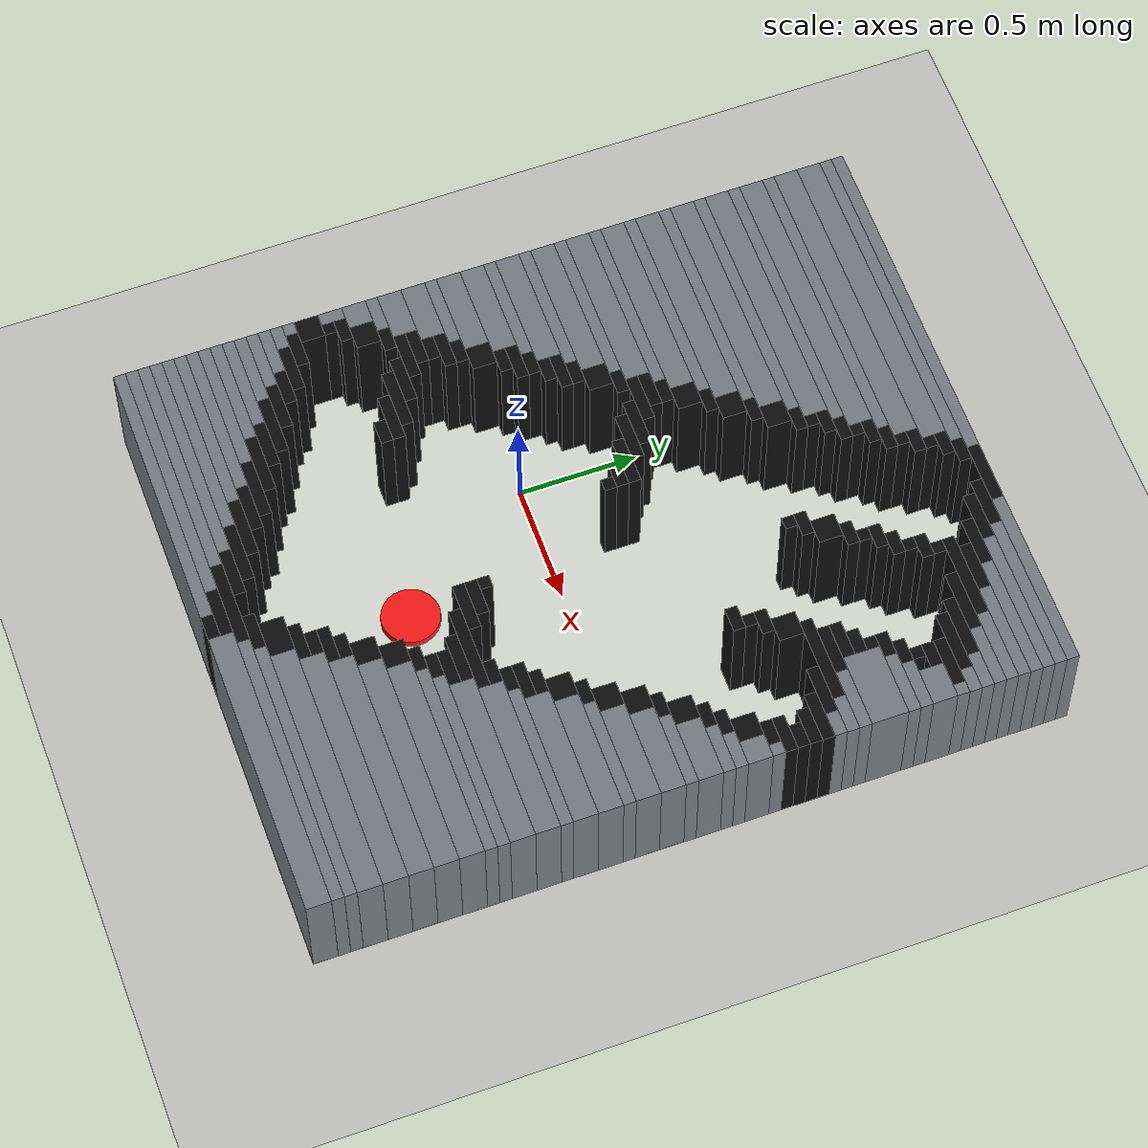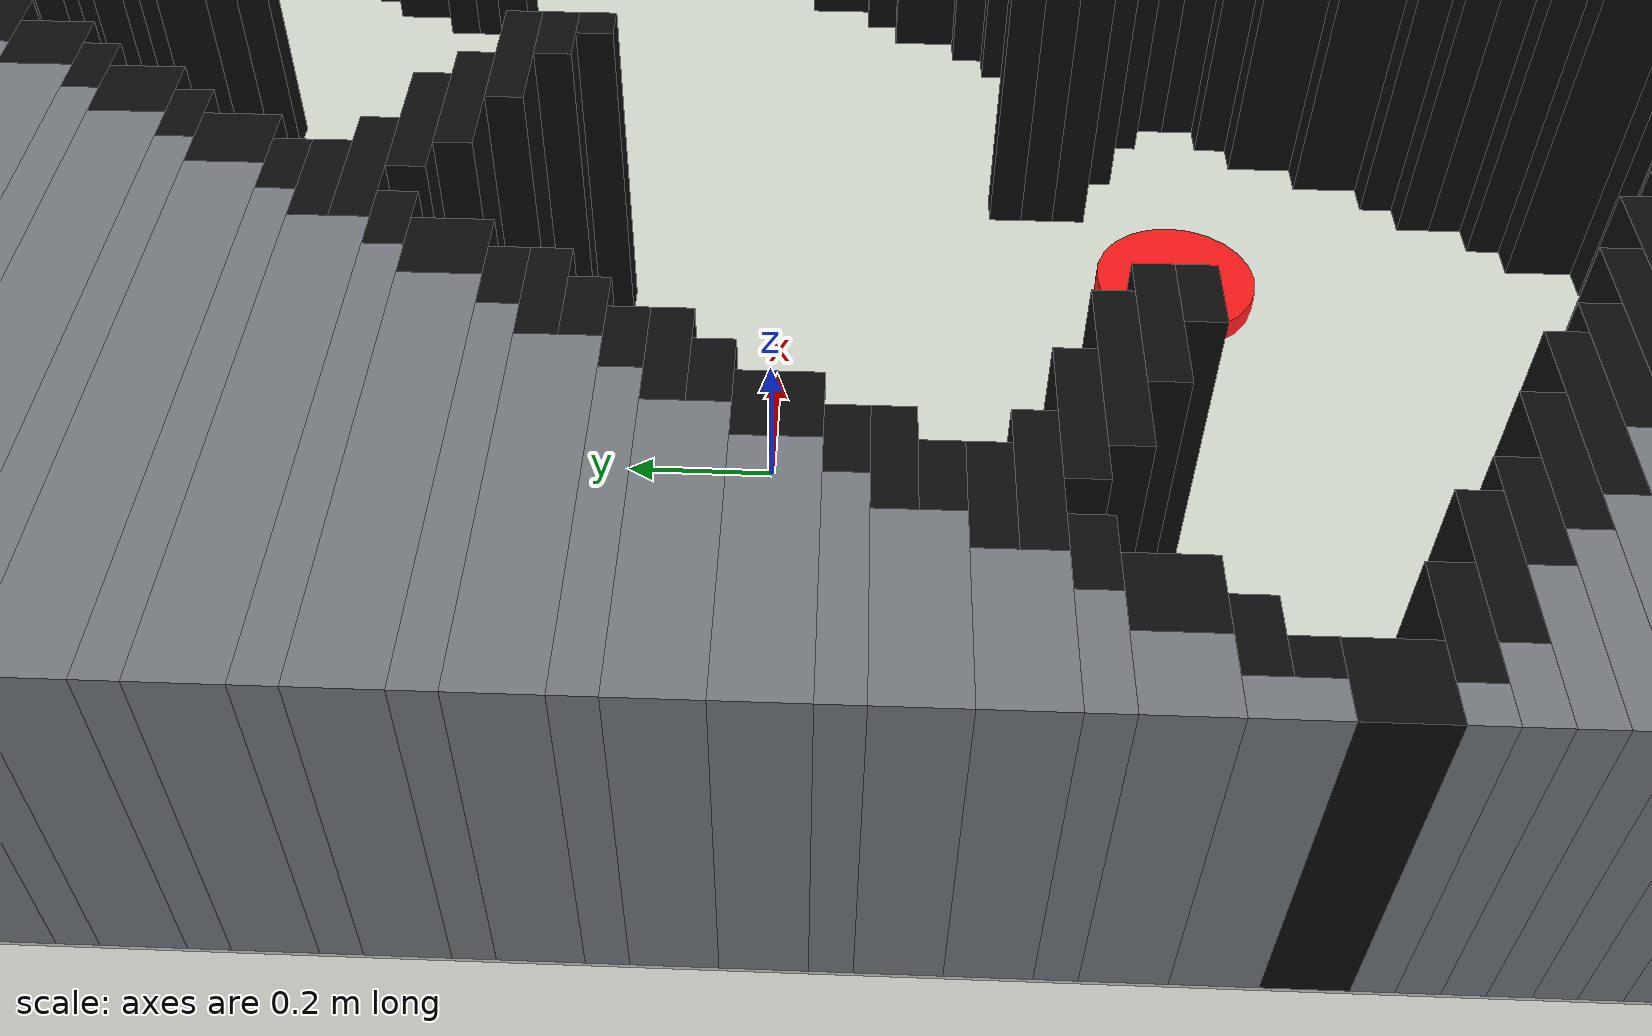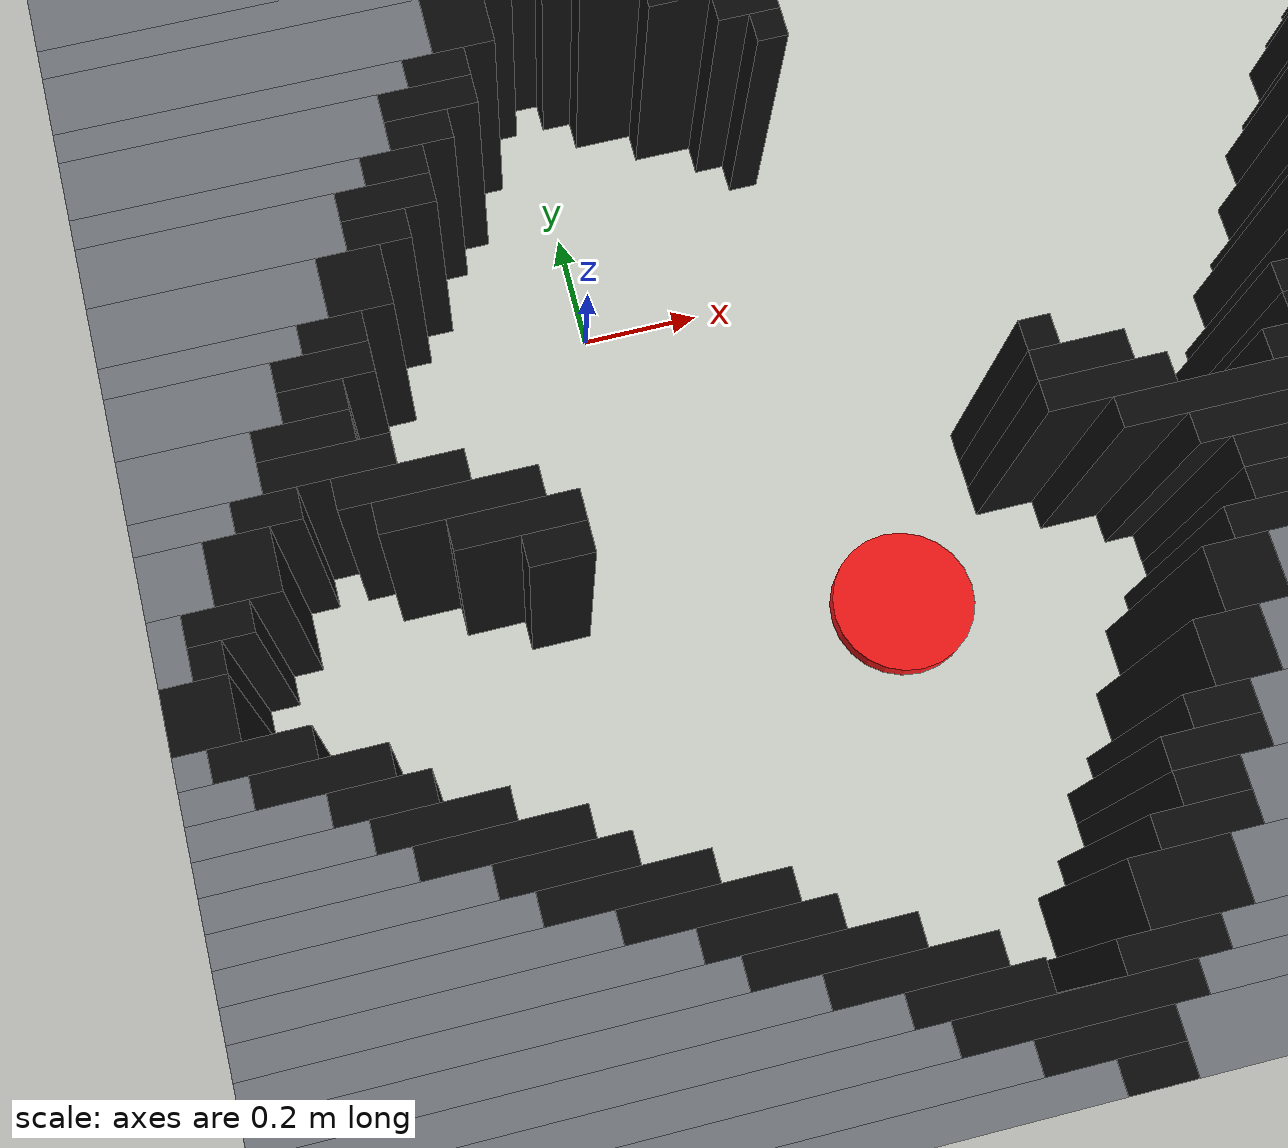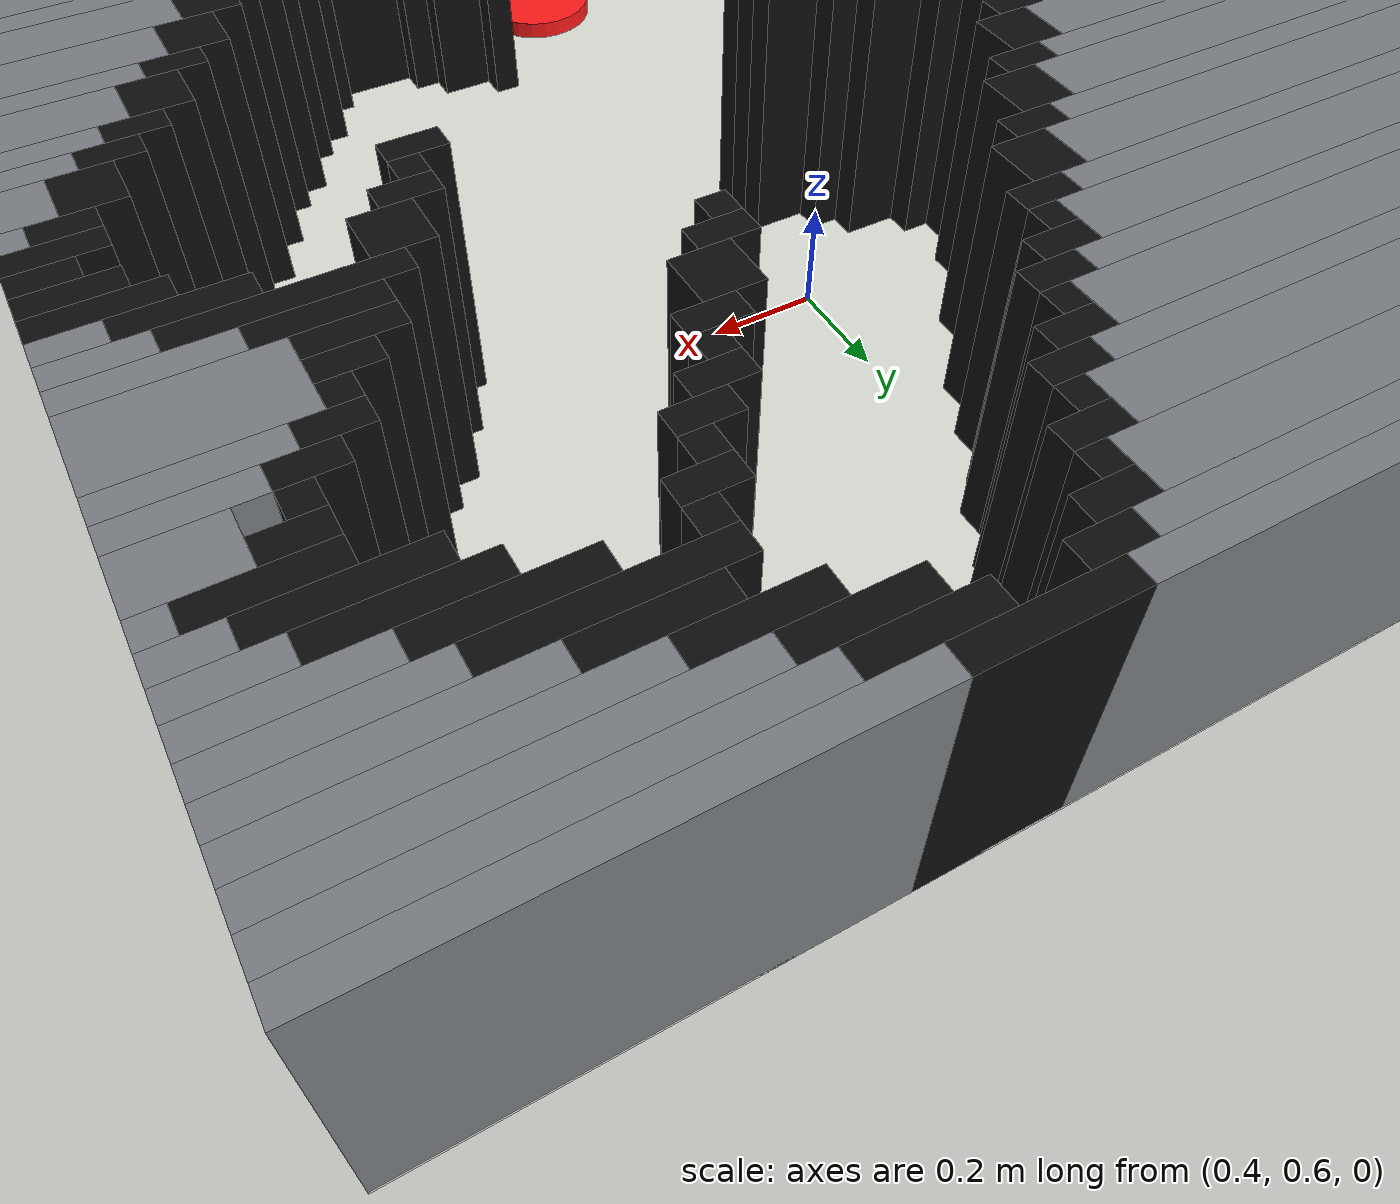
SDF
<sdf version="1.9">
 <world name="two_tb4_lab">
  <plugin filename="gz-sim-physics-system" name="gz::sim::systems::Physics"/>
  <plugin filename="gz-sim-user-commands-system" name="gz::sim::systems::UserCommands"/>
  <plugin filename="gz-sim-scene-broadcaster-system" name="gz::sim::systems::SceneBroadcaster"/>
  <physics name="stable_step" type="ignored">
   <max_step_size>0.005</max_step_size>
   <real_time_factor>1.0</real_time_factor>
  </physics>
  <scene><ambient>0.4 0.4 0.4 1</ambient><background>0.8 0.85 0.9 1</background><shadows>false</shadows></scene>
  <model name="ground_plane">
   <static>true</static>
   <link name="link">
    <collision name="collision">
     <geometry><plane><normal>0 0 1</normal><size>5 5</size></plane></geometry>
    </collision>
    <visual name="visual">
     <geometry><plane><normal>0 0 1</normal><size>5 5</size></plane></geometry>
     <material><ambient>0.78 0.78 0.76 1</ambient><diffuse>0.78 0.78 0.76 1</diffuse></material>
    </visual>
   </link>
  </model>
  <model name="lab_map_floor">
   <static>true</static>
   <pose>0.450 0.125 0.003 0 0 0</pose>
   <link name="link">
    <visual name="visual">
     <geometry><box><size>2.450 3.100 0.006</size></box></geometry>
     <material><ambient>0.86 0.88 0.84 1</ambient><diffuse>0.86 0.88 0.84 1</diffuse></material>
    </visual>
   </link>
  </model>
  <model name="lab_occupied_cells">
   <static>true</static>
   <link name="lab_occupied_cells_000">
    <pose>0.425 -1.400 0.250 0 0 0</pose>
    <collision name="collision"><geometry><box><size>0.100 0.050 0.500</size></box></geometry></collision>
    <visual name="visual">
     <geometry><box><size>0.100 0.050 0.500</size></box></geometry>
     <material><ambient>0.05 0.05 0.05 1</ambient><diffuse>0.05 0.05 0.05 1</diffuse></material>
    </visual>
   </link>
   <link name="lab_occupied_cells_001">
    <pose>0.375 -1.350 0.250 0 0 0</pose>
    <collision name="collision"><geometry><box><size>0.200 0.050 0.500</size></box></geometry></collision>
    <visual name="visual">
     <geometry><box><size>0.200 0.050 0.500</size></box></geometry>
     <material><ambient>0.05 0.05 0.05 1</ambient><diffuse>0.05 0.05 0.05 1</diffuse></material>
    </visual>
   </link>
   <link name="lab_occupied_cells_002">
    <pose>0.350 -1.300 0.250 0 0 0</pose>
    <collision name="collision"><geometry><box><size>0.350 0.050 0.500</size></box></geometry></collision>
    <visual name="visual">
     <geometry><box><size>0.350 0.050 0.500</size></box></geometry>
     <material><ambient>0.05 0.05 0.05 1</ambient><diffuse>0.05 0.05 0.05 1</diffuse></material>
    </visual>
   </link>
   <link name="lab_occupied_cells_003">
    <pose>0.225 -1.250 0.250 0 0 0</pose>
    <collision name="collision"><geometry><box><size>0.200 0.050 0.500</size></box></geometry></collision>
    <visual name="visual">
     <geometry><box><size>0.200 0.050 0.500</size></box></geometry>
     <material><ambient>0.05 0.05 0.05 1</ambient><diffuse>0.05 0.05 0.05 1</diffuse></material>
    </visual>
   </link>
   <link name="lab_occupied_cells_004">
    <pose>0.500 -1.250 0.250 0 0 0</pose>
    <collision name="collision"><geometry><box><size>0.150 0.050 0.500</size></box></geometry></collision>
    <visual name="visual">
     <geometry><box><size>0.150 0.050 0.500</size></box></geometry>
     <material><ambient>0.05 0.05 0.05 1</ambient><diffuse>0.05 0.05 0.05 1</diffuse></material>
    </visual>
   </link>
   <link name="lab_occupied_cells_005">
    <pose>0.150 -1.200 0.250 0 0 0</pose>
    <collision name="collision"><geometry><box><size>0.250 0.050 0.500</size></box></geometry></collision>
    <visual name="visual">
     <geometry><box><size>0.250 0.050 0.500</size></box></geometry>
     <material><ambient>0.05 0.05 0.05 1</ambient><diffuse>0.05 0.05 0.05 1</diffuse></material>
    </visual>
   </link>
   <link name="lab_occupied_cells_006">
    <pose>0.550 -1.175 0.250 0 0 0</pose>
    <collision name="collision"><geometry><box><size>0.150 0.100 0.500</size></box></geometry></collision>
    <visual name="visual">
     <geometry><box><size>0.150 0.100 0.500</size></box></geometry>
     <material><ambient>0.05 0.05 0.05 1</ambient><diffuse>0.05 0.05 0.05 1</diffuse></material>
    </visual>
   </link>
   <link name="lab_occupied_cells_007">
    <pose>0.050 -1.150 0.250 0 0 0</pose>
    <collision name="collision"><geometry><box><size>0.250 0.050 0.500</size></box></geometry></collision>
    <visual name="visual">
     <geometry><box><size>0.250 0.050 0.500</size></box></geometry>
     <material><ambient>0.05 0.05 0.05 1</ambient><diffuse>0.05 0.05 0.05 1</diffuse></material>
    </visual>
   </link>
   <link name="lab_occupied_cells_008">
    <pose>-0.025 -1.100 0.250 0 0 0</pose>
    <collision name="collision"><geometry><box><size>0.200 0.050 0.500</size></box></geometry></collision>
    <visual name="visual">
     <geometry><box><size>0.200 0.050 0.500</size></box></geometry>
     <material><ambient>0.05 0.05 0.05 1</ambient><diffuse>0.05 0.05 0.05 1</diffuse></material>
    </visual>
   </link>
   <link name="lab_occupied_cells_009">
    <pose>0.600 -1.100 0.250 0 0 0</pose>
    <collision name="collision"><geometry><box><size>0.150 0.050 0.500</size></box></geometry></collision>
    <visual name="visual">
     <geometry><box><size>0.150 0.050 0.500</size></box></geometry>
     <material><ambient>0.05 0.05 0.05 1</ambient><diffuse>0.05 0.05 0.05 1</diffuse></material>
    </visual>
   </link>
   <link name="lab_occupied_cells_010">
    <pose>-0.100 -1.050 0.250 0 0 0</pose>
    <collision name="collision"><geometry><box><size>0.250 0.050 0.500</size></box></geometry></collision>
    <visual name="visual">
     <geometry><box><size>0.250 0.050 0.500</size></box></geometry>
     <material><ambient>0.05 0.05 0.05 1</ambient><diffuse>0.05 0.05 0.05 1</diffuse></material>
    </visual>
   </link>
   <link name="lab_occupied_cells_011">
    <pose>0.625 -1.050 0.250 0 0 0</pose>
    <collision name="collision"><geometry><box><size>0.100 0.050 0.500</size></box></geometry></collision>
    <visual name="visual">
     <geometry><box><size>0.100 0.050 0.500</size></box></geometry>
     <material><ambient>0.05 0.05 0.05 1</ambient><diffuse>0.05 0.05 0.05 1</diffuse></material>
    </visual>
   </link>
   <link name="lab_occupied_cells_012">
    <pose>-0.200 -1.000 0.250 0 0 0</pose>
    <collision name="collision"><geometry><box><size>0.250 0.050 0.500</size></box></geometry></collision>
    <visual name="visual">
     <geometry><box><size>0.250 0.050 0.500</size></box></geometry>
     <material><ambient>0.05 0.05 0.05 1</ambient><diffuse>0.05 0.05 0.05 1</diffuse></material>
    </visual>
   </link>
   <link name="lab_occupied_cells_013">
    <pose>0.650 -1.000 0.250 0 0 0</pose>
    <collision name="collision"><geometry><box><size>0.150 0.050 0.500</size></box></geometry></collision>
    <visual name="visual">
     <geometry><box><size>0.150 0.050 0.500</size></box></geometry>
     <material><ambient>0.05 0.05 0.05 1</ambient><diffuse>0.05 0.05 0.05 1</diffuse></material>
    </visual>
   </link>
   <link name="lab_occupied_cells_014">
    <pose>-0.275 -0.950 0.250 0 0 0</pose>
    <collision name="collision"><geometry><box><size>0.200 0.050 0.500</size></box></geometry></collision>
    <visual name="visual">
     <geometry><box><size>0.200 0.050 0.500</size></box></geometry>
     <material><ambient>0.05 0.05 0.05 1</ambient><diffuse>0.05 0.05 0.05 1</diffuse></material>
    </visual>
   </link>
   <link name="lab_occupied_cells_015">
    <pose>0.675 -0.950 0.250 0 0 0</pose>
    <collision name="collision"><geometry><box><size>0.100 0.050 0.500</size></box></geometry></collision>
    <visual name="visual">
     <geometry><box><size>0.100 0.050 0.500</size></box></geometry>
     <material><ambient>0.05 0.05 0.05 1</ambient><diffuse>0.05 0.05 0.05 1</diffuse></material>
    </visual>
   </link>
   <link name="lab_occupied_cells_016">
    <pose>-0.350 -0.900 0.250 0 0 0</pose>
    <collision name="collision"><geometry><box><size>0.250 0.050 0.500</size></box></geometry></collision>
    <visual name="visual">
     <geometry><box><size>0.250 0.050 0.500</size></box></geometry>
     <material><ambient>0.05 0.05 0.05 1</ambient><diffuse>0.05 0.05 0.05 1</diffuse></material>
    </visual>
   </link>
   <link name="lab_occupied_cells_017">
    <pose>0.725 -0.875 0.250 0 0 0</pose>
    <collision name="collision"><geometry><box><size>0.100 0.100 0.500</size></box></geometry></collision>
    <visual name="visual">
     <geometry><box><size>0.100 0.100 0.500</size></box></geometry>
     <material><ambient>0.05 0.05 0.05 1</ambient><diffuse>0.05 0.05 0.05 1</diffuse></material>
    </visual>
   </link>
   <link name="lab_occupied_cells_018">
    <pose>-0.425 -0.850 0.250 0 0 0</pose>
    <collision name="collision"><geometry><box><size>0.200 0.050 0.500</size></box></geometry></collision>
    <visual name="visual">
     <geometry><box><size>0.200 0.050 0.500</size></box></geometry>
     <material><ambient>0.05 0.05 0.05 1</ambient><diffuse>0.05 0.05 0.05 1</diffuse></material>
    </visual>
   </link>
   <link name="lab_occupied_cells_019">
    <pose>-0.500 -0.800 0.250 0 0 0</pose>
    <collision name="collision"><geometry><box><size>0.150 0.050 0.500</size></box></geometry></collision>
    <visual name="visual">
     <geometry><box><size>0.150 0.050 0.500</size></box></geometry>
     <material><ambient>0.05 0.05 0.05 1</ambient><diffuse>0.05 0.05 0.05 1</diffuse></material>
    </visual>
   </link>
   <link name="lab_occupied_cells_020">
    <pose>0.775 -0.775 0.250 0 0 0</pose>
    <collision name="collision"><geometry><box><size>0.100 0.100 0.500</size></box></geometry></collision>
    <visual name="visual">
     <geometry><box><size>0.100 0.100 0.500</size></box></geometry>
     <material><ambient>0.05 0.05 0.05 1</ambient><diffuse>0.05 0.05 0.05 1</diffuse></material>
    </visual>
   </link>
   <link name="lab_occupied_cells_021">
    <pose>-0.575 -0.750 0.250 0 0 0</pose>
    <collision name="collision"><geometry><box><size>0.200 0.050 0.500</size></box></geometry></collision>
    <visual name="visual">
     <geometry><box><size>0.200 0.050 0.500</size></box></geometry>
     <material><ambient>0.05 0.05 0.05 1</ambient><diffuse>0.05 0.05 0.05 1</diffuse></material>
    </visual>
   </link>
   <link name="lab_occupied_cells_022">
    <pose>-0.650 -0.700 0.250 0 0 0</pose>
    <collision name="collision"><geometry><box><size>0.150 0.050 0.500</size></box></geometry></collision>
    <visual name="visual">
     <geometry><box><size>0.150 0.050 0.500</size></box></geometry>
     <material><ambient>0.05 0.05 0.05 1</ambient><diffuse>0.05 0.05 0.05 1</diffuse></material>
    </visual>
   </link>
   <link name="lab_occupied_cells_023">
    <pose>0.825 -0.700 0.250 0 0 0</pose>
    <collision name="collision"><geometry><box><size>0.100 0.050 0.500</size></box></geometry></collision>
    <visual name="visual">
     <geometry><box><size>0.100 0.050 0.500</size></box></geometry>
     <material><ambient>0.05 0.05 0.05 1</ambient><diffuse>0.05 0.05 0.05 1</diffuse></material>
    </visual>
   </link>
   <link name="lab_occupied_cells_024">
    <pose>0.875 -0.650 0.250 0 0 0</pose>
    <collision name="collision"><geometry><box><size>0.100 0.050 0.500</size></box></geometry></collision>
    <visual name="visual">
     <geometry><box><size>0.100 0.050 0.500</size></box></geometry>
     <material><ambient>0.05 0.05 0.05 1</ambient><diffuse>0.05 0.05 0.05 1</diffuse></material>
    </visual>
   </link>
   <link name="lab_occupied_cells_025">
    <pose>-0.725 -0.625 0.250 0 0 0</pose>
    <collision name="collision"><geometry><box><size>0.100 0.100 0.500</size></box></geometry></collision>
    <visual name="visual">
     <geometry><box><size>0.100 0.100 0.500</size></box></geometry>
     <material><ambient>0.05 0.05 0.05 1</ambient><diffuse>0.05 0.05 0.05 1</diffuse></material>
    </visual>
   </link>
   <link name="lab_occupied_cells_026">
    <pose>0.900 -0.600 0.250 0 0 0</pose>
    <collision name="collision"><geometry><box><size>0.150 0.050 0.500</size></box></geometry></collision>
    <visual name="visual">
     <geometry><box><size>0.150 0.050 0.500</size></box></geometry>
     <material><ambient>0.05 0.05 0.05 1</ambient><diffuse>0.05 0.05 0.05 1</diffuse></material>
    </visual>
   </link>
   <link name="lab_occupied_cells_027">
    <pose>-0.700 -0.550 0.250 0 0 0</pose>
    <collision name="collision"><geometry><box><size>0.050 0.050 0.500</size></box></geometry></collision>
    <visual name="visual">
     <geometry><box><size>0.050 0.050 0.500</size></box></geometry>
     <material><ambient>0.05 0.05 0.05 1</ambient><diffuse>0.05 0.05 0.05 1</diffuse></material>
    </visual>
   </link>
   <link name="lab_occupied_cells_028">
    <pose>0.875 -0.550 0.250 0 0 0</pose>
    <collision name="collision"><geometry><box><size>0.200 0.050 0.500</size></box></geometry></collision>
    <visual name="visual">
     <geometry><box><size>0.200 0.050 0.500</size></box></geometry>
     <material><ambient>0.05 0.05 0.05 1</ambient><diffuse>0.05 0.05 0.05 1</diffuse></material>
    </visual>
   </link>
   <link name="lab_occupied_cells_029">
    <pose>-0.675 -0.500 0.250 0 0 0</pose>
    <collision name="collision"><geometry><box><size>0.100 0.050 0.500</size></box></geometry></collision>
    <visual name="visual">
     <geometry><box><size>0.100 0.050 0.500</size></box></geometry>
     <material><ambient>0.05 0.05 0.05 1</ambient><diffuse>0.05 0.05 0.05 1</diffuse></material>
    </visual>
   </link>
   <link name="lab_occupied_cells_030">
    <pose>-0.175 -0.500 0.250 0 0 0</pose>
    <collision name="collision"><geometry><box><size>0.100 0.050 0.500</size></box></geometry></collision>
    <visual name="visual">
     <geometry><box><size>0.100 0.050 0.500</size></box></geometry>
     <material><ambient>0.05 0.05 0.05 1</ambient><diffuse>0.05 0.05 0.05 1</diffuse></material>
    </visual>
   </link>
   <link name="lab_occupied_cells_031">
    <pose>0.850 -0.500 0.250 0 0 0</pose>
    <collision name="collision"><geometry><box><size>0.350 0.050 0.500</size></box></geometry></collision>
    <visual name="visual">
     <geometry><box><size>0.350 0.050 0.500</size></box></geometry>
     <material><ambient>0.05 0.05 0.05 1</ambient><diffuse>0.05 0.05 0.05 1</diffuse></material>
    </visual>
   </link>
   <link name="lab_occupied_cells_032">
    <pose>-0.225 -0.450 0.250 0 0 0</pose>
    <collision name="collision"><geometry><box><size>0.200 0.050 0.500</size></box></geometry></collision>
    <visual name="visual">
     <geometry><box><size>0.200 0.050 0.500</size></box></geometry>
     <material><ambient>0.05 0.05 0.05 1</ambient><diffuse>0.05 0.05 0.05 1</diffuse></material>
    </visual>
   </link>
   <link name="lab_occupied_cells_033">
    <pose>0.675 -0.450 0.250 0 0 0</pose>
    <collision name="collision"><geometry><box><size>0.200 0.050 0.500</size></box></geometry></collision>
    <visual name="visual">
     <geometry><box><size>0.200 0.050 0.500</size></box></geometry>
     <material><ambient>0.05 0.05 0.05 1</ambient><diffuse>0.05 0.05 0.05 1</diffuse></material>
    </visual>
   </link>
   <link name="lab_occupied_cells_034">
    <pose>0.975 -0.450 0.250 0 0 0</pose>
    <collision name="collision"><geometry><box><size>0.100 0.050 0.500</size></box></geometry></collision>
    <visual name="visual">
     <geometry><box><size>0.100 0.050 0.500</size></box></geometry>
     <material><ambient>0.05 0.05 0.05 1</ambient><diffuse>0.05 0.05 0.05 1</diffuse></material>
    </visual>
   </link>
   <link name="lab_occupied_cells_035">
    <pose>-0.625 -0.425 0.250 0 0 0</pose>
    <collision name="collision"><geometry><box><size>0.100 0.100 0.500</size></box></geometry></collision>
    <visual name="visual">
     <geometry><box><size>0.100 0.100 0.500</size></box></geometry>
     <material><ambient>0.05 0.05 0.05 1</ambient><diffuse>0.05 0.05 0.05 1</diffuse></material>
    </visual>
   </link>
   <link name="lab_occupied_cells_036">
    <pose>-0.300 -0.400 0.250 0 0 0</pose>
    <collision name="collision"><geometry><box><size>0.250 0.050 0.500</size></box></geometry></collision>
    <visual name="visual">
     <geometry><box><size>0.250 0.050 0.500</size></box></geometry>
     <material><ambient>0.05 0.05 0.05 1</ambient><diffuse>0.05 0.05 0.05 1</diffuse></material>
    </visual>
   </link>
   <link name="lab_occupied_cells_037">
    <pose>0.650 -0.400 0.250 0 0 0</pose>
    <collision name="collision"><geometry><box><size>0.150 0.050 0.500</size></box></geometry></collision>
    <visual name="visual">
     <geometry><box><size>0.150 0.050 0.500</size></box></geometry>
     <material><ambient>0.05 0.05 0.05 1</ambient><diffuse>0.05 0.05 0.05 1</diffuse></material>
    </visual>
   </link>
   <link name="lab_occupied_cells_038">
    <pose>1.025 -0.400 0.250 0 0 0</pose>
    <collision name="collision"><geometry><box><size>0.100 0.050 0.500</size></box></geometry></collision>
    <visual name="visual">
     <geometry><box><size>0.100 0.050 0.500</size></box></geometry>
     <material><ambient>0.05 0.05 0.05 1</ambient><diffuse>0.05 0.05 0.05 1</diffuse></material>
    </visual>
   </link>
   <link name="lab_occupied_cells_039">
    <pose>-0.575 -0.350 0.250 0 0 0</pose>
    <collision name="collision"><geometry><box><size>0.100 0.050 0.500</size></box></geometry></collision>
    <visual name="visual">
     <geometry><box><size>0.100 0.050 0.500</size></box></geometry>
     <material><ambient>0.05 0.05 0.05 1</ambient><diffuse>0.05 0.05 0.05 1</diffuse></material>
    </visual>
   </link>
   <link name="lab_occupied_cells_040">
    <pose>-0.375 -0.350 0.250 0 0 0</pose>
    <collision name="collision"><geometry><box><size>0.200 0.050 0.500</size></box></geometry></collision>
    <visual name="visual">
     <geometry><box><size>0.200 0.050 0.500</size></box></geometry>
     <material><ambient>0.05 0.05 0.05 1</ambient><diffuse>0.05 0.05 0.05 1</diffuse></material>
    </visual>
   </link>
   <link name="lab_occupied_cells_041">
    <pose>0.600 -0.350 0.250 0 0 0</pose>
    <collision name="collision"><geometry><box><size>0.050 0.050 0.500</size></box></geometry></collision>
    <visual name="visual">
     <geometry><box><size>0.050 0.050 0.500</size></box></geometry>
     <material><ambient>0.05 0.05 0.05 1</ambient><diffuse>0.05 0.05 0.05 1</diffuse></material>
    </visual>
   </link>
   <link name="lab_occupied_cells_042">
    <pose>1.050 -0.350 0.250 0 0 0</pose>
    <collision name="collision"><geometry><box><size>0.150 0.050 0.500</size></box></geometry></collision>
    <visual name="visual">
     <geometry><box><size>0.150 0.050 0.500</size></box></geometry>
     <material><ambient>0.05 0.05 0.05 1</ambient><diffuse>0.05 0.05 0.05 1</diffuse></material>
    </visual>
   </link>
   <link name="lab_occupied_cells_043">
    <pose>-0.475 -0.300 0.250 0 0 0</pose>
    <collision name="collision"><geometry><box><size>0.200 0.050 0.500</size></box></geometry></collision>
    <visual name="visual">
     <geometry><box><size>0.200 0.050 0.500</size></box></geometry>
     <material><ambient>0.05 0.05 0.05 1</ambient><diffuse>0.05 0.05 0.05 1</diffuse></material>
    </visual>
   </link>
   <link name="lab_occupied_cells_044">
    <pose>1.075 -0.300 0.250 0 0 0</pose>
    <collision name="collision"><geometry><box><size>0.100 0.050 0.500</size></box></geometry></collision>
    <visual name="visual">
     <geometry><box><size>0.100 0.050 0.500</size></box></geometry>
     <material><ambient>0.05 0.05 0.05 1</ambient><diffuse>0.05 0.05 0.05 1</diffuse></material>
    </visual>
   </link>
   <link name="lab_occupied_cells_045">
    <pose>-0.500 -0.250 0.250 0 0 0</pose>
    <collision name="collision"><geometry><box><size>0.150 0.050 0.500</size></box></geometry></collision>
    <visual name="visual">
     <geometry><box><size>0.150 0.050 0.500</size></box></geometry>
     <material><ambient>0.05 0.05 0.05 1</ambient><diffuse>0.05 0.05 0.05 1</diffuse></material>
    </visual>
   </link>
   <link name="lab_occupied_cells_046">
    <pose>1.125 -0.225 0.250 0 0 0</pose>
    <collision name="collision"><geometry><box><size>0.100 0.100 0.500</size></box></geometry></collision>
    <visual name="visual">
     <geometry><box><size>0.100 0.100 0.500</size></box></geometry>
     <material><ambient>0.05 0.05 0.05 1</ambient><diffuse>0.05 0.05 0.05 1</diffuse></material>
    </visual>
   </link>
   <link name="lab_occupied_cells_047">
    <pose>-0.475 -0.200 0.250 0 0 0</pose>
    <collision name="collision"><geometry><box><size>0.100 0.050 0.500</size></box></geometry></collision>
    <visual name="visual">
     <geometry><box><size>0.100 0.050 0.500</size></box></geometry>
     <material><ambient>0.05 0.05 0.05 1</ambient><diffuse>0.05 0.05 0.05 1</diffuse></material>
    </visual>
   </link>
   <link name="lab_occupied_cells_048">
    <pose>-0.450 -0.150 0.250 0 0 0</pose>
    <collision name="collision"><geometry><box><size>0.150 0.050 0.500</size></box></geometry></collision>
    <visual name="visual">
     <geometry><box><size>0.150 0.050 0.500</size></box></geometry>
     <material><ambient>0.05 0.05 0.05 1</ambient><diffuse>0.05 0.05 0.05 1</diffuse></material>
    </visual>
   </link>
   <link name="lab_occupied_cells_049">
    <pose>1.175 -0.150 0.250 0 0 0</pose>
    <collision name="collision"><geometry><box><size>0.100 0.050 0.500</size></box></geometry></collision>
    <visual name="visual">
     <geometry><box><size>0.100 0.050 0.500</size></box></geometry>
     <material><ambient>0.05 0.05 0.05 1</ambient><diffuse>0.05 0.05 0.05 1</diffuse></material>
    </visual>
   </link>
   <link name="lab_occupied_cells_050">
    <pose>-0.425 -0.100 0.250 0 0 0</pose>
    <collision name="collision"><geometry><box><size>0.100 0.050 0.500</size></box></geometry></collision>
    <visual name="visual">
     <geometry><box><size>0.100 0.050 0.500</size></box></geometry>
     <material><ambient>0.05 0.05 0.05 1</ambient><diffuse>0.05 0.05 0.05 1</diffuse></material>
    </visual>
   </link>
   <link name="lab_occupied_cells_051">
    <pose>1.225 -0.075 0.250 0 0 0</pose>
    <collision name="collision"><geometry><box><size>0.100 0.100 0.500</size></box></geometry></collision>
    <visual name="visual">
     <geometry><box><size>0.100 0.100 0.500</size></box></geometry>
     <material><ambient>0.05 0.05 0.05 1</ambient><diffuse>0.05 0.05 0.05 1</diffuse></material>
    </visual>
   </link>
   <link name="lab_occupied_cells_052">
    <pose>-0.375 -0.025 0.250 0 0 0</pose>
    <collision name="collision"><geometry><box><size>0.100 0.100 0.500</size></box></geometry></collision>
    <visual name="visual">
     <geometry><box><size>0.100 0.100 0.500</size></box></geometry>
     <material><ambient>0.05 0.05 0.05 1</ambient><diffuse>0.05 0.05 0.05 1</diffuse></material>
    </visual>
   </link>
   <link name="lab_occupied_cells_053">
    <pose>1.275 0.025 0.250 0 0 0</pose>
    <collision name="collision"><geometry><box><size>0.100 0.100 0.500</size></box></geometry></collision>
    <visual name="visual">
     <geometry><box><size>0.100 0.100 0.500</size></box></geometry>
     <material><ambient>0.05 0.05 0.05 1</ambient><diffuse>0.05 0.05 0.05 1</diffuse></material>
    </visual>
   </link>
   <link name="lab_occupied_cells_054">
    <pose>-0.325 0.050 0.250 0 0 0</pose>
    <collision name="collision"><geometry><box><size>0.100 0.050 0.500</size></box></geometry></collision>
    <visual name="visual">
     <geometry><box><size>0.100 0.050 0.500</size></box></geometry>
     <material><ambient>0.05 0.05 0.05 1</ambient><diffuse>0.05 0.05 0.05 1</diffuse></material>
    </visual>
   </link>
   <link name="lab_occupied_cells_055">
    <pose>-0.300 0.100 0.250 0 0 0</pose>
    <collision name="collision"><geometry><box><size>0.150 0.050 0.500</size></box></geometry></collision>
    <visual name="visual">
     <geometry><box><size>0.150 0.050 0.500</size></box></geometry>
     <material><ambient>0.05 0.05 0.05 1</ambient><diffuse>0.05 0.05 0.05 1</diffuse></material>
    </visual>
   </link>
   <link name="lab_occupied_cells_056">
    <pose>1.325 0.100 0.250 0 0 0</pose>
    <collision name="collision"><geometry><box><size>0.100 0.050 0.500</size></box></geometry></collision>
    <visual name="visual">
     <geometry><box><size>0.100 0.050 0.500</size></box></geometry>
     <material><ambient>0.05 0.05 0.05 1</ambient><diffuse>0.05 0.05 0.05 1</diffuse></material>
    </visual>
   </link>
   <link name="lab_occupied_cells_057">
    <pose>-0.275 0.150 0.250 0 0 0</pose>
    <collision name="collision"><geometry><box><size>0.100 0.050 0.500</size></box></geometry></collision>
    <visual name="visual">
     <geometry><box><size>0.100 0.050 0.500</size></box></geometry>
     <material><ambient>0.05 0.05 0.05 1</ambient><diffuse>0.05 0.05 0.05 1</diffuse></material>
    </visual>
   </link>
   <link name="lab_occupied_cells_058">
    <pose>1.375 0.175 0.250 0 0 0</pose>
    <collision name="collision"><geometry><box><size>0.100 0.100 0.500</size></box></geometry></collision>
    <visual name="visual">
     <geometry><box><size>0.100 0.100 0.500</size></box></geometry>
     <material><ambient>0.05 0.05 0.05 1</ambient><diffuse>0.05 0.05 0.05 1</diffuse></material>
    </visual>
   </link>
   <link name="lab_occupied_cells_059">
    <pose>-0.225 0.200 0.250 0 0 0</pose>
    <collision name="collision"><geometry><box><size>0.100 0.050 0.500</size></box></geometry></collision>
    <visual name="visual">
     <geometry><box><size>0.100 0.050 0.500</size></box></geometry>
     <material><ambient>0.05 0.05 0.05 1</ambient><diffuse>0.05 0.05 0.05 1</diffuse></material>
    </visual>
   </link>
   <link name="lab_occupied_cells_060">
    <pose>-0.200 0.250 0.250 0 0 0</pose>
    <collision name="collision"><geometry><box><size>0.150 0.050 0.500</size></box></geometry></collision>
    <visual name="visual">
     <geometry><box><size>0.150 0.050 0.500</size></box></geometry>
     <material><ambient>0.05 0.05 0.05 1</ambient><diffuse>0.05 0.05 0.05 1</diffuse></material>
    </visual>
   </link>
   <link name="lab_occupied_cells_061">
    <pose>0.350 0.250 0.250 0 0 0</pose>
    <collision name="collision"><geometry><box><size>0.050 0.050 0.500</size></box></geometry></collision>
    <visual name="visual">
     <geometry><box><size>0.050 0.050 0.500</size></box></geometry>
     <material><ambient>0.05 0.05 0.05 1</ambient><diffuse>0.05 0.05 0.05 1</diffuse></material>
    </visual>
   </link>
   <link name="lab_occupied_cells_062">
    <pose>1.425 0.250 0.250 0 0 0</pose>
    <collision name="collision"><geometry><box><size>0.100 0.050 0.500</size></box></geometry></collision>
    <visual name="visual">
     <geometry><box><size>0.100 0.050 0.500</size></box></geometry>
     <material><ambient>0.05 0.05 0.05 1</ambient><diffuse>0.05 0.05 0.05 1</diffuse></material>
    </visual>
   </link>
   <link name="lab_occupied_cells_063">
    <pose>-0.175 0.300 0.250 0 0 0</pose>
    <collision name="collision"><geometry><box><size>0.100 0.050 0.500</size></box></geometry></collision>
    <visual name="visual">
     <geometry><box><size>0.100 0.050 0.500</size></box></geometry>
     <material><ambient>0.05 0.05 0.05 1</ambient><diffuse>0.05 0.05 0.05 1</diffuse></material>
    </visual>
   </link>
   <link name="lab_occupied_cells_064">
    <pose>0.325 0.300 0.250 0 0 0</pose>
    <collision name="collision"><geometry><box><size>0.100 0.050 0.500</size></box></geometry></collision>
    <visual name="visual">
     <geometry><box><size>0.100 0.050 0.500</size></box></geometry>
     <material><ambient>0.05 0.05 0.05 1</ambient><diffuse>0.05 0.05 0.05 1</diffuse></material>
    </visual>
   </link>
   <link name="lab_occupied_cells_065">
    <pose>1.475 0.300 0.250 0 0 0</pose>
    <collision name="collision"><geometry><box><size>0.100 0.050 0.500</size></box></geometry></collision>
    <visual name="visual">
     <geometry><box><size>0.100 0.050 0.500</size></box></geometry>
     <material><ambient>0.05 0.05 0.05 1</ambient><diffuse>0.05 0.05 0.05 1</diffuse></material>
    </visual>
   </link>
   <link name="lab_occupied_cells_066">
    <pose>0.275 0.350 0.250 0 0 0</pose>
    <collision name="collision"><geometry><box><size>0.200 0.050 0.500</size></box></geometry></collision>
    <visual name="visual">
     <geometry><box><size>0.200 0.050 0.500</size></box></geometry>
     <material><ambient>0.05 0.05 0.05 1</ambient><diffuse>0.05 0.05 0.05 1</diffuse></material>
    </visual>
   </link>
   <link name="lab_occupied_cells_067">
    <pose>-0.125 0.375 0.250 0 0 0</pose>
    <collision name="collision"><geometry><box><size>0.100 0.100 0.500</size></box></geometry></collision>
    <visual name="visual">
     <geometry><box><size>0.100 0.100 0.500</size></box></geometry>
     <material><ambient>0.05 0.05 0.05 1</ambient><diffuse>0.05 0.05 0.05 1</diffuse></material>
    </visual>
   </link>
   <link name="lab_occupied_cells_068">
    <pose>1.525 0.375 0.250 0 0 0</pose>
    <collision name="collision"><geometry><box><size>0.100 0.100 0.500</size></box></geometry></collision>
    <visual name="visual">
     <geometry><box><size>0.100 0.100 0.500</size></box></geometry>
     <material><ambient>0.05 0.05 0.05 1</ambient><diffuse>0.05 0.05 0.05 1</diffuse></material>
    </visual>
   </link>
   <link name="lab_occupied_cells_069">
    <pose>0.175 0.400 0.250 0 0 0</pose>
    <collision name="collision"><geometry><box><size>0.200 0.050 0.500</size></box></geometry></collision>
    <visual name="visual">
     <geometry><box><size>0.200 0.050 0.500</size></box></geometry>
     <material><ambient>0.05 0.05 0.05 1</ambient><diffuse>0.05 0.05 0.05 1</diffuse></material>
    </visual>
   </link>
   <link name="lab_occupied_cells_070">
    <pose>-0.075 0.450 0.250 0 0 0</pose>
    <collision name="collision"><geometry><box><size>0.100 0.050 0.500</size></box></geometry></collision>
    <visual name="visual">
     <geometry><box><size>0.100 0.050 0.500</size></box></geometry>
     <material><ambient>0.05 0.05 0.05 1</ambient><diffuse>0.05 0.05 0.05 1</diffuse></material>
    </visual>
   </link>
   <link name="lab_occupied_cells_071">
    <pose>0.125 0.450 0.250 0 0 0</pose>
    <collision name="collision"><geometry><box><size>0.200 0.050 0.500</size></box></geometry></collision>
    <visual name="visual">
     <geometry><box><size>0.200 0.050 0.500</size></box></geometry>
     <material><ambient>0.05 0.05 0.05 1</ambient><diffuse>0.05 0.05 0.05 1</diffuse></material>
    </visual>
   </link>
   <link name="lab_occupied_cells_072">
    <pose>1.575 0.450 0.250 0 0 0</pose>
    <collision name="collision"><geometry><box><size>0.100 0.050 0.500</size></box></geometry></collision>
    <visual name="visual">
     <geometry><box><size>0.100 0.050 0.500</size></box></geometry>
     <material><ambient>0.05 0.05 0.05 1</ambient><diffuse>0.05 0.05 0.05 1</diffuse></material>
    </visual>
   </link>
   <link name="lab_occupied_cells_073">
    <pose>0.025 0.500 0.250 0 0 0</pose>
    <collision name="collision"><geometry><box><size>0.200 0.050 0.500</size></box></geometry></collision>
    <visual name="visual">
     <geometry><box><size>0.200 0.050 0.500</size></box></geometry>
     <material><ambient>0.05 0.05 0.05 1</ambient><diffuse>0.05 0.05 0.05 1</diffuse></material>
    </visual>
   </link>
   <link name="lab_occupied_cells_074">
    <pose>1.075 0.500 0.250 0 0 0</pose>
    <collision name="collision"><geometry><box><size>0.100 0.050 0.500</size></box></geometry></collision>
    <visual name="visual">
     <geometry><box><size>0.100 0.050 0.500</size></box></geometry>
     <material><ambient>0.05 0.05 0.05 1</ambient><diffuse>0.05 0.05 0.05 1</diffuse></material>
    </visual>
   </link>
   <link name="lab_occupied_cells_075">
    <pose>1.600 0.500 0.250 0 0 0</pose>
    <collision name="collision"><geometry><box><size>0.150 0.050 0.500</size></box></geometry></collision>
    <visual name="visual">
     <geometry><box><size>0.150 0.050 0.500</size></box></geometry>
     <material><ambient>0.05 0.05 0.05 1</ambient><diffuse>0.05 0.05 0.05 1</diffuse></material>
    </visual>
   </link>
   <link name="lab_occupied_cells_076">
    <pose>0.000 0.550 0.250 0 0 0</pose>
    <collision name="collision"><geometry><box><size>0.150 0.050 0.500</size></box></geometry></collision>
    <visual name="visual">
     <geometry><box><size>0.150 0.050 0.500</size></box></geometry>
     <material><ambient>0.05 0.05 0.05 1</ambient><diffuse>0.05 0.05 0.05 1</diffuse></material>
    </visual>
   </link>
   <link name="lab_occupied_cells_077">
    <pose>1.100 0.550 0.250 0 0 0</pose>
    <collision name="collision"><geometry><box><size>0.050 0.050 0.500</size></box></geometry></collision>
    <visual name="visual">
     <geometry><box><size>0.050 0.050 0.500</size></box></geometry>
     <material><ambient>0.05 0.05 0.05 1</ambient><diffuse>0.05 0.05 0.05 1</diffuse></material>
    </visual>
   </link>
   <link name="lab_occupied_cells_078">
    <pose>1.625 0.550 0.250 0 0 0</pose>
    <collision name="collision"><geometry><box><size>0.100 0.050 0.500</size></box></geometry></collision>
    <visual name="visual">
     <geometry><box><size>0.100 0.050 0.500</size></box></geometry>
     <material><ambient>0.05 0.05 0.05 1</ambient><diffuse>0.05 0.05 0.05 1</diffuse></material>
    </visual>
   </link>
   <link name="lab_occupied_cells_079">
    <pose>0.025 0.600 0.250 0 0 0</pose>
    <collision name="collision"><geometry><box><size>0.100 0.050 0.500</size></box></geometry></collision>
    <visual name="visual">
     <geometry><box><size>0.100 0.050 0.500</size></box></geometry>
     <material><ambient>0.05 0.05 0.05 1</ambient><diffuse>0.05 0.05 0.05 1</diffuse></material>
    </visual>
   </link>
   <link name="lab_occupied_cells_080">
    <pose>1.125 0.600 0.250 0 0 0</pose>
    <collision name="collision"><geometry><box><size>0.100 0.050 0.500</size></box></geometry></collision>
    <visual name="visual">
     <geometry><box><size>0.100 0.050 0.500</size></box></geometry>
     <material><ambient>0.05 0.05 0.05 1</ambient><diffuse>0.05 0.05 0.05 1</diffuse></material>
    </visual>
   </link>
   <link name="lab_occupied_cells_081">
    <pose>1.600 0.600 0.250 0 0 0</pose>
    <collision name="collision"><geometry><box><size>0.150 0.050 0.500</size></box></geometry></collision>
    <visual name="visual">
     <geometry><box><size>0.150 0.050 0.500</size></box></geometry>
     <material><ambient>0.05 0.05 0.05 1</ambient><diffuse>0.05 0.05 0.05 1</diffuse></material>
    </visual>
   </link>
   <link name="lab_occupied_cells_082">
    <pose>1.575 0.650 0.250 0 0 0</pose>
    <collision name="collision"><geometry><box><size>0.200 0.050 0.500</size></box></geometry></collision>
    <visual name="visual">
     <geometry><box><size>0.200 0.050 0.500</size></box></geometry>
     <material><ambient>0.05 0.05 0.05 1</ambient><diffuse>0.05 0.05 0.05 1</diffuse></material>
    </visual>
   </link>
   <link name="lab_occupied_cells_083">
    <pose>0.075 0.675 0.250 0 0 0</pose>
    <collision name="collision"><geometry><box><size>0.100 0.100 0.500</size></box></geometry></collision>
    <visual name="visual">
     <geometry><box><size>0.100 0.100 0.500</size></box></geometry>
     <material><ambient>0.05 0.05 0.05 1</ambient><diffuse>0.05 0.05 0.05 1</diffuse></material>
    </visual>
   </link>
   <link name="lab_occupied_cells_084">
    <pose>1.175 0.675 0.250 0 0 0</pose>
    <collision name="collision"><geometry><box><size>0.100 0.100 0.500</size></box></geometry></collision>
    <visual name="visual">
     <geometry><box><size>0.100 0.100 0.500</size></box></geometry>
     <material><ambient>0.05 0.05 0.05 1</ambient><diffuse>0.05 0.05 0.05 1</diffuse></material>
    </visual>
   </link>
   <link name="lab_occupied_cells_085">
    <pose>1.475 0.700 0.250 0 0 0</pose>
    <collision name="collision"><geometry><box><size>0.200 0.050 0.500</size></box></geometry></collision>
    <visual name="visual">
     <geometry><box><size>0.200 0.050 0.500</size></box></geometry>
     <material><ambient>0.05 0.05 0.05 1</ambient><diffuse>0.05 0.05 0.05 1</diffuse></material>
    </visual>
   </link>
   <link name="lab_occupied_cells_086">
    <pose>0.125 0.750 0.250 0 0 0</pose>
    <collision name="collision"><geometry><box><size>0.100 0.050 0.500</size></box></geometry></collision>
    <visual name="visual">
     <geometry><box><size>0.100 0.050 0.500</size></box></geometry>
     <material><ambient>0.05 0.05 0.05 1</ambient><diffuse>0.05 0.05 0.05 1</diffuse></material>
    </visual>
   </link>
   <link name="lab_occupied_cells_087">
    <pose>1.350 0.750 0.250 0 0 0</pose>
    <collision name="collision"><geometry><box><size>0.350 0.050 0.500</size></box></geometry></collision>
    <visual name="visual">
     <geometry><box><size>0.350 0.050 0.500</size></box></geometry>
     <material><ambient>0.05 0.05 0.05 1</ambient><diffuse>0.05 0.05 0.05 1</diffuse></material>
    </visual>
   </link>
   <link name="lab_occupied_cells_088">
    <pose>1.325 0.800 0.250 0 0 0</pose>
    <collision name="collision"><geometry><box><size>0.200 0.050 0.500</size></box></geometry></collision>
    <visual name="visual">
     <geometry><box><size>0.200 0.050 0.500</size></box></geometry>
     <material><ambient>0.05 0.05 0.05 1</ambient><diffuse>0.05 0.05 0.05 1</diffuse></material>
    </visual>
   </link>
   <link name="lab_occupied_cells_089">
    <pose>0.175 0.825 0.250 0 0 0</pose>
    <collision name="collision"><geometry><box><size>0.100 0.100 0.500</size></box></geometry></collision>
    <visual name="visual">
     <geometry><box><size>0.100 0.100 0.500</size></box></geometry>
     <material><ambient>0.05 0.05 0.05 1</ambient><diffuse>0.05 0.05 0.05 1</diffuse></material>
    </visual>
   </link>
   <link name="lab_occupied_cells_090">
    <pose>0.750 0.850 0.250 0 0 0</pose>
    <collision name="collision"><geometry><box><size>0.050 0.050 0.500</size></box></geometry></collision>
    <visual name="visual">
     <geometry><box><size>0.050 0.050 0.500</size></box></geometry>
     <material><ambient>0.05 0.05 0.05 1</ambient><diffuse>0.05 0.05 0.05 1</diffuse></material>
    </visual>
   </link>
   <link name="lab_occupied_cells_091">
    <pose>1.300 0.850 0.250 0 0 0</pose>
    <collision name="collision"><geometry><box><size>0.150 0.050 0.500</size></box></geometry></collision>
    <visual name="visual">
     <geometry><box><size>0.150 0.050 0.500</size></box></geometry>
     <material><ambient>0.05 0.05 0.05 1</ambient><diffuse>0.05 0.05 0.05 1</diffuse></material>
    </visual>
   </link>
   <link name="lab_occupied_cells_092">
    <pose>0.225 0.900 0.250 0 0 0</pose>
    <collision name="collision"><geometry><box><size>0.100 0.050 0.500</size></box></geometry></collision>
    <visual name="visual">
     <geometry><box><size>0.100 0.050 0.500</size></box></geometry>
     <material><ambient>0.05 0.05 0.05 1</ambient><diffuse>0.05 0.05 0.05 1</diffuse></material>
    </visual>
   </link>
   <link name="lab_occupied_cells_093">
    <pose>0.775 0.900 0.250 0 0 0</pose>
    <collision name="collision"><geometry><box><size>0.100 0.050 0.500</size></box></geometry></collision>
    <visual name="visual">
     <geometry><box><size>0.100 0.050 0.500</size></box></geometry>
     <material><ambient>0.05 0.05 0.05 1</ambient><diffuse>0.05 0.05 0.05 1</diffuse></material>
    </visual>
   </link>
   <link name="lab_occupied_cells_094">
    <pose>1.325 0.900 0.250 0 0 0</pose>
    <collision name="collision"><geometry><box><size>0.100 0.050 0.500</size></box></geometry></collision>
    <visual name="visual">
     <geometry><box><size>0.100 0.050 0.500</size></box></geometry>
     <material><ambient>0.05 0.05 0.05 1</ambient><diffuse>0.05 0.05 0.05 1</diffuse></material>
    </visual>
   </link>
   <link name="lab_occupied_cells_095">
    <pose>1.350 0.950 0.250 0 0 0</pose>
    <collision name="collision"><geometry><box><size>0.050 0.050 0.500</size></box></geometry></collision>
    <visual name="visual">
     <geometry><box><size>0.050 0.050 0.500</size></box></geometry>
     <material><ambient>0.05 0.05 0.05 1</ambient><diffuse>0.05 0.05 0.05 1</diffuse></material>
    </visual>
   </link>
   <link name="lab_occupied_cells_096">
    <pose>0.275 0.975 0.250 0 0 0</pose>
    <collision name="collision"><geometry><box><size>0.100 0.100 0.500</size></box></geometry></collision>
    <visual name="visual">
     <geometry><box><size>0.100 0.100 0.500</size></box></geometry>
     <material><ambient>0.05 0.05 0.05 1</ambient><diffuse>0.05 0.05 0.05 1</diffuse></material>
    </visual>
   </link>
   <link name="lab_occupied_cells_097">
    <pose>0.825 0.975 0.250 0 0 0</pose>
    <collision name="collision"><geometry><box><size>0.100 0.100 0.500</size></box></geometry></collision>
    <visual name="visual">
     <geometry><box><size>0.100 0.100 0.500</size></box></geometry>
     <material><ambient>0.05 0.05 0.05 1</ambient><diffuse>0.05 0.05 0.05 1</diffuse></material>
    </visual>
   </link>
   <link name="lab_occupied_cells_098">
    <pose>1.375 1.000 0.250 0 0 0</pose>
    <collision name="collision"><geometry><box><size>0.100 0.050 0.500</size></box></geometry></collision>
    <visual name="visual">
     <geometry><box><size>0.100 0.050 0.500</size></box></geometry>
     <material><ambient>0.05 0.05 0.05 1</ambient><diffuse>0.05 0.05 0.05 1</diffuse></material>
    </visual>
   </link>
   <link name="lab_occupied_cells_099">
    <pose>0.325 1.050 0.250 0 0 0</pose>
    <collision name="collision"><geometry><box><size>0.100 0.050 0.500</size></box></geometry></collision>
    <visual name="visual">
     <geometry><box><size>0.100 0.050 0.500</size></box></geometry>
     <material><ambient>0.05 0.05 0.05 1</ambient><diffuse>0.05 0.05 0.05 1</diffuse></material>
    </visual>
   </link>
   <link name="lab_occupied_cells_100">
    <pose>0.875 1.050 0.250 0 0 0</pose>
    <collision name="collision"><geometry><box><size>0.100 0.050 0.500</size></box></geometry></collision>
    <visual name="visual">
     <geometry><box><size>0.100 0.050 0.500</size></box></geometry>
     <material><ambient>0.05 0.05 0.05 1</ambient><diffuse>0.05 0.05 0.05 1</diffuse></material>
    </visual>
   </link>
   <link name="lab_occupied_cells_101">
    <pose>1.425 1.050 0.250 0 0 0</pose>
    <collision name="collision"><geometry><box><size>0.100 0.050 0.500</size></box></geometry></collision>
    <visual name="visual">
     <geometry><box><size>0.100 0.050 0.500</size></box></geometry>
     <material><ambient>0.05 0.05 0.05 1</ambient><diffuse>0.05 0.05 0.05 1</diffuse></material>
    </visual>
   </link>
   <link name="lab_occupied_cells_102">
    <pose>0.350 1.100 0.250 0 0 0</pose>
    <collision name="collision"><geometry><box><size>0.050 0.050 0.500</size></box></geometry></collision>
    <visual name="visual">
     <geometry><box><size>0.050 0.050 0.500</size></box></geometry>
     <material><ambient>0.05 0.05 0.05 1</ambient><diffuse>0.05 0.05 0.05 1</diffuse></material>
    </visual>
   </link>
   <link name="lab_occupied_cells_103">
    <pose>0.900 1.100 0.250 0 0 0</pose>
    <collision name="collision"><geometry><box><size>0.050 0.050 0.500</size></box></geometry></collision>
    <visual name="visual">
     <geometry><box><size>0.050 0.050 0.500</size></box></geometry>
     <material><ambient>0.05 0.05 0.05 1</ambient><diffuse>0.05 0.05 0.05 1</diffuse></material>
    </visual>
   </link>
   <link name="lab_occupied_cells_104">
    <pose>1.450 1.100 0.250 0 0 0</pose>
    <collision name="collision"><geometry><box><size>0.050 0.050 0.500</size></box></geometry></collision>
    <visual name="visual">
     <geometry><box><size>0.050 0.050 0.500</size></box></geometry>
     <material><ambient>0.05 0.05 0.05 1</ambient><diffuse>0.05 0.05 0.05 1</diffuse></material>
    </visual>
   </link>
   <link name="lab_occupied_cells_105">
    <pose>0.375 1.150 0.250 0 0 0</pose>
    <collision name="collision"><geometry><box><size>0.100 0.050 0.500</size></box></geometry></collision>
    <visual name="visual">
     <geometry><box><size>0.100 0.050 0.500</size></box></geometry>
     <material><ambient>0.05 0.05 0.05 1</ambient><diffuse>0.05 0.05 0.05 1</diffuse></material>
    </visual>
   </link>
   <link name="lab_occupied_cells_106">
    <pose>0.925 1.150 0.250 0 0 0</pose>
    <collision name="collision"><geometry><box><size>0.100 0.050 0.500</size></box></geometry></collision>
    <visual name="visual">
     <geometry><box><size>0.100 0.050 0.500</size></box></geometry>
     <material><ambient>0.05 0.05 0.05 1</ambient><diffuse>0.05 0.05 0.05 1</diffuse></material>
    </visual>
   </link>
   <link name="lab_occupied_cells_107">
    <pose>1.475 1.150 0.250 0 0 0</pose>
    <collision name="collision"><geometry><box><size>0.100 0.050 0.500</size></box></geometry></collision>
    <visual name="visual">
     <geometry><box><size>0.100 0.050 0.500</size></box></geometry>
     <material><ambient>0.05 0.05 0.05 1</ambient><diffuse>0.05 0.05 0.05 1</diffuse></material>
    </visual>
   </link>
   <link name="lab_occupied_cells_108">
    <pose>0.425 1.200 0.250 0 0 0</pose>
    <collision name="collision"><geometry><box><size>0.100 0.050 0.500</size></box></geometry></collision>
    <visual name="visual">
     <geometry><box><size>0.100 0.050 0.500</size></box></geometry>
     <material><ambient>0.05 0.05 0.05 1</ambient><diffuse>0.05 0.05 0.05 1</diffuse></material>
    </visual>
   </link>
   <link name="lab_occupied_cells_109">
    <pose>0.975 1.200 0.250 0 0 0</pose>
    <collision name="collision"><geometry><box><size>0.100 0.050 0.500</size></box></geometry></collision>
    <visual name="visual">
     <geometry><box><size>0.100 0.050 0.500</size></box></geometry>
     <material><ambient>0.05 0.05 0.05 1</ambient><diffuse>0.05 0.05 0.05 1</diffuse></material>
    </visual>
   </link>
   <link name="lab_occupied_cells_110">
    <pose>1.525 1.200 0.250 0 0 0</pose>
    <collision name="collision"><geometry><box><size>0.200 0.050 0.500</size></box></geometry></collision>
    <visual name="visual">
     <geometry><box><size>0.200 0.050 0.500</size></box></geometry>
     <material><ambient>0.05 0.05 0.05 1</ambient><diffuse>0.05 0.05 0.05 1</diffuse></material>
    </visual>
   </link>
   <link name="lab_occupied_cells_111">
    <pose>0.450 1.250 0.250 0 0 0</pose>
    <collision name="collision"><geometry><box><size>0.050 0.050 0.500</size></box></geometry></collision>
    <visual name="visual">
     <geometry><box><size>0.050 0.050 0.500</size></box></geometry>
     <material><ambient>0.05 0.05 0.05 1</ambient><diffuse>0.05 0.05 0.05 1</diffuse></material>
    </visual>
   </link>
   <link name="lab_occupied_cells_112">
    <pose>1.000 1.250 0.250 0 0 0</pose>
    <collision name="collision"><geometry><box><size>0.050 0.050 0.500</size></box></geometry></collision>
    <visual name="visual">
     <geometry><box><size>0.050 0.050 0.500</size></box></geometry>
     <material><ambient>0.05 0.05 0.05 1</ambient><diffuse>0.05 0.05 0.05 1</diffuse></material>
    </visual>
   </link>
   <link name="lab_occupied_cells_113">
    <pose>1.450 1.250 0.250 0 0 0</pose>
    <collision name="collision"><geometry><box><size>0.250 0.050 0.500</size></box></geometry></collision>
    <visual name="visual">
     <geometry><box><size>0.250 0.050 0.500</size></box></geometry>
     <material><ambient>0.05 0.05 0.05 1</ambient><diffuse>0.05 0.05 0.05 1</diffuse></material>
    </visual>
   </link>
   <link name="lab_occupied_cells_114">
    <pose>0.475 1.300 0.250 0 0 0</pose>
    <collision name="collision"><geometry><box><size>0.100 0.050 0.500</size></box></geometry></collision>
    <visual name="visual">
     <geometry><box><size>0.100 0.050 0.500</size></box></geometry>
     <material><ambient>0.05 0.05 0.05 1</ambient><diffuse>0.05 0.05 0.05 1</diffuse></material>
    </visual>
   </link>
   <link name="lab_occupied_cells_115">
    <pose>1.025 1.300 0.250 0 0 0</pose>
    <collision name="collision"><geometry><box><size>0.100 0.050 0.500</size></box></geometry></collision>
    <visual name="visual">
     <geometry><box><size>0.100 0.050 0.500</size></box></geometry>
     <material><ambient>0.05 0.05 0.05 1</ambient><diffuse>0.05 0.05 0.05 1</diffuse></material>
    </visual>
   </link>
   <link name="lab_occupied_cells_116">
    <pose>1.400 1.300 0.250 0 0 0</pose>
    <collision name="collision"><geometry><box><size>0.250 0.050 0.500</size></box></geometry></collision>
    <visual name="visual">
     <geometry><box><size>0.250 0.050 0.500</size></box></geometry>
     <material><ambient>0.05 0.05 0.05 1</ambient><diffuse>0.05 0.05 0.05 1</diffuse></material>
    </visual>
   </link>
   <link name="lab_occupied_cells_117">
    <pose>0.525 1.350 0.250 0 0 0</pose>
    <collision name="collision"><geometry><box><size>0.100 0.050 0.500</size></box></geometry></collision>
    <visual name="visual">
     <geometry><box><size>0.100 0.050 0.500</size></box></geometry>
     <material><ambient>0.05 0.05 0.05 1</ambient><diffuse>0.05 0.05 0.05 1</diffuse></material>
    </visual>
   </link>
   <link name="lab_occupied_cells_118">
    <pose>1.050 1.350 0.250 0 0 0</pose>
    <collision name="collision"><geometry><box><size>0.050 0.050 0.500</size></box></geometry></collision>
    <visual name="visual">
     <geometry><box><size>0.050 0.050 0.500</size></box></geometry>
     <material><ambient>0.05 0.05 0.05 1</ambient><diffuse>0.05 0.05 0.05 1</diffuse></material>
    </visual>
   </link>
   <link name="lab_occupied_cells_119">
    <pose>1.300 1.350 0.250 0 0 0</pose>
    <collision name="collision"><geometry><box><size>0.250 0.050 0.500</size></box></geometry></collision>
    <visual name="visual">
     <geometry><box><size>0.250 0.050 0.500</size></box></geometry>
     <material><ambient>0.05 0.05 0.05 1</ambient><diffuse>0.05 0.05 0.05 1</diffuse></material>
    </visual>
   </link>
   <link name="lab_occupied_cells_120">
    <pose>0.550 1.400 0.250 0 0 0</pose>
    <collision name="collision"><geometry><box><size>0.050 0.050 0.500</size></box></geometry></collision>
    <visual name="visual">
     <geometry><box><size>0.050 0.050 0.500</size></box></geometry>
     <material><ambient>0.05 0.05 0.05 1</ambient><diffuse>0.05 0.05 0.05 1</diffuse></material>
    </visual>
   </link>
   <link name="lab_occupied_cells_121">
    <pose>1.200 1.400 0.250 0 0 0</pose>
    <collision name="collision"><geometry><box><size>0.350 0.050 0.500</size></box></geometry></collision>
    <visual name="visual">
     <geometry><box><size>0.350 0.050 0.500</size></box></geometry>
     <material><ambient>0.05 0.05 0.05 1</ambient><diffuse>0.05 0.05 0.05 1</diffuse></material>
    </visual>
   </link>
   <link name="lab_occupied_cells_122">
    <pose>0.575 1.450 0.250 0 0 0</pose>
    <collision name="collision"><geometry><box><size>0.100 0.050 0.500</size></box></geometry></collision>
    <visual name="visual">
     <geometry><box><size>0.100 0.050 0.500</size></box></geometry>
     <material><ambient>0.05 0.05 0.05 1</ambient><diffuse>0.05 0.05 0.05 1</diffuse></material>
    </visual>
   </link>
   <link name="lab_occupied_cells_123">
    <pose>1.175 1.450 0.250 0 0 0</pose>
    <collision name="collision"><geometry><box><size>0.200 0.050 0.500</size></box></geometry></collision>
    <visual name="visual">
     <geometry><box><size>0.200 0.050 0.500</size></box></geometry>
     <material><ambient>0.05 0.05 0.05 1</ambient><diffuse>0.05 0.05 0.05 1</diffuse></material>
    </visual>
   </link>
   <link name="lab_occupied_cells_124">
    <pose>0.600 1.500 0.250 0 0 0</pose>
    <collision name="collision"><geometry><box><size>0.050 0.050 0.500</size></box></geometry></collision>
    <visual name="visual">
     <geometry><box><size>0.050 0.050 0.500</size></box></geometry>
     <material><ambient>0.05 0.05 0.05 1</ambient><diffuse>0.05 0.05 0.05 1</diffuse></material>
    </visual>
   </link>
   <link name="lab_occupied_cells_125">
    <pose>1.075 1.500 0.250 0 0 0</pose>
    <collision name="collision"><geometry><box><size>0.200 0.050 0.500</size></box></geometry></collision>
    <visual name="visual">
     <geometry><box><size>0.200 0.050 0.500</size></box></geometry>
     <material><ambient>0.05 0.05 0.05 1</ambient><diffuse>0.05 0.05 0.05 1</diffuse></material>
    </visual>
   </link>
   <link name="lab_occupied_cells_126">
    <pose>0.625 1.550 0.250 0 0 0</pose>
    <collision name="collision"><geometry><box><size>0.100 0.050 0.500</size></box></geometry></collision>
    <visual name="visual">
     <geometry><box><size>0.100 0.050 0.500</size></box></geometry>
     <material><ambient>0.05 0.05 0.05 1</ambient><diffuse>0.05 0.05 0.05 1</diffuse></material>
    </visual>
   </link>
   <link name="lab_occupied_cells_127">
    <pose>0.975 1.550 0.250 0 0 0</pose>
    <collision name="collision"><geometry><box><size>0.200 0.050 0.500</size></box></geometry></collision>
    <visual name="visual">
     <geometry><box><size>0.200 0.050 0.500</size></box></geometry>
     <material><ambient>0.05 0.05 0.05 1</ambient><diffuse>0.05 0.05 0.05 1</diffuse></material>
    </visual>
   </link>
   <link name="lab_occupied_cells_128">
    <pose>0.675 1.600 0.250 0 0 0</pose>
    <collision name="collision"><geometry><box><size>0.100 0.050 0.500</size></box></geometry></collision>
    <visual name="visual">
     <geometry><box><size>0.100 0.050 0.500</size></box></geometry>
     <material><ambient>0.05 0.05 0.05 1</ambient><diffuse>0.05 0.05 0.05 1</diffuse></material>
    </visual>
   </link>
   <link name="lab_occupied_cells_129">
    <pose>0.925 1.600 0.250 0 0 0</pose>
    <collision name="collision"><geometry><box><size>0.200 0.050 0.500</size></box></geometry></collision>
    <visual name="visual">
     <geometry><box><size>0.200 0.050 0.500</size></box></geometry>
     <material><ambient>0.05 0.05 0.05 1</ambient><diffuse>0.05 0.05 0.05 1</diffuse></material>
    </visual>
   </link>
   <link name="lab_occupied_cells_130">
    <pose>0.800 1.650 0.250 0 0 0</pose>
    <collision name="collision"><geometry><box><size>0.250 0.050 0.500</size></box></geometry></collision>
    <visual name="visual">
     <geometry><box><size>0.250 0.050 0.500</size></box></geometry>
     <material><ambient>0.05 0.05 0.05 1</ambient><diffuse>0.05 0.05 0.05 1</diffuse></material>
    </visual>
   </link>
  </model>
  <model name="lab_unknown_cells">
   <static>true</static>
   <link name="lab_unknown_cells_000">
    <pose>-0.200 -1.400 0.250 0 0 0</pose>
    <collision name="collision"><geometry><box><size>1.150 0.050 0.500</size></box></geometry></collision>
    <visual name="visual">
     <geometry><box><size>1.150 0.050 0.500</size></box></geometry>
     <material><ambient>0.48 0.50 0.52 1</ambient><diffuse>0.48 0.50 0.52 1</diffuse></material>
    </visual>
   </link>
   <link name="lab_unknown_cells_001">
    <pose>1.075 -1.375 0.250 0 0 0</pose>
    <collision name="collision"><geometry><box><size>1.200 0.100 0.500</size></box></geometry></collision>
    <visual name="visual">
     <geometry><box><size>1.200 0.100 0.500</size></box></geometry>
     <material><ambient>0.48 0.50 0.52 1</ambient><diffuse>0.48 0.50 0.52 1</diffuse></material>
    </visual>
   </link>
   <link name="lab_unknown_cells_002">
    <pose>-0.250 -1.350 0.250 0 0 0</pose>
    <collision name="collision"><geometry><box><size>1.050 0.050 0.500</size></box></geometry></collision>
    <visual name="visual">
     <geometry><box><size>1.050 0.050 0.500</size></box></geometry>
     <material><ambient>0.48 0.50 0.52 1</ambient><diffuse>0.48 0.50 0.52 1</diffuse></material>
    </visual>
   </link>
   <link name="lab_unknown_cells_003">
    <pose>-0.300 -1.300 0.250 0 0 0</pose>
    <collision name="collision"><geometry><box><size>0.950 0.050 0.500</size></box></geometry></collision>
    <visual name="visual">
     <geometry><box><size>0.950 0.050 0.500</size></box></geometry>
     <material><ambient>0.48 0.50 0.52 1</ambient><diffuse>0.48 0.50 0.52 1</diffuse></material>
    </visual>
   </link>
   <link name="lab_unknown_cells_004">
    <pose>1.100 -1.300 0.250 0 0 0</pose>
    <collision name="collision"><geometry><box><size>1.150 0.050 0.500</size></box></geometry></collision>
    <visual name="visual">
     <geometry><box><size>1.150 0.050 0.500</size></box></geometry>
     <material><ambient>0.48 0.50 0.52 1</ambient><diffuse>0.48 0.50 0.52 1</diffuse></material>
    </visual>
   </link>
   <link name="lab_unknown_cells_005">
    <pose>-0.325 -1.250 0.250 0 0 0</pose>
    <collision name="collision"><geometry><box><size>0.900 0.050 0.500</size></box></geometry></collision>
    <visual name="visual">
     <geometry><box><size>0.900 0.050 0.500</size></box></geometry>
     <material><ambient>0.48 0.50 0.52 1</ambient><diffuse>0.48 0.50 0.52 1</diffuse></material>
    </visual>
   </link>
   <link name="lab_unknown_cells_006">
    <pose>1.125 -1.250 0.250 0 0 0</pose>
    <collision name="collision"><geometry><box><size>1.100 0.050 0.500</size></box></geometry></collision>
    <visual name="visual">
     <geometry><box><size>1.100 0.050 0.500</size></box></geometry>
     <material><ambient>0.48 0.50 0.52 1</ambient><diffuse>0.48 0.50 0.52 1</diffuse></material>
    </visual>
   </link>
   <link name="lab_unknown_cells_007">
    <pose>-0.375 -1.200 0.250 0 0 0</pose>
    <collision name="collision"><geometry><box><size>0.800 0.050 0.500</size></box></geometry></collision>
    <visual name="visual">
     <geometry><box><size>0.800 0.050 0.500</size></box></geometry>
     <material><ambient>0.48 0.50 0.52 1</ambient><diffuse>0.48 0.50 0.52 1</diffuse></material>
    </visual>
   </link>
   <link name="lab_unknown_cells_008">
    <pose>1.150 -1.175 0.250 0 0 0</pose>
    <collision name="collision"><geometry><box><size>1.050 0.100 0.500</size></box></geometry></collision>
    <visual name="visual">
     <geometry><box><size>1.050 0.100 0.500</size></box></geometry>
     <material><ambient>0.48 0.50 0.52 1</ambient><diffuse>0.48 0.50 0.52 1</diffuse></material>
    </visual>
   </link>
   <link name="lab_unknown_cells_009">
    <pose>-0.425 -1.150 0.250 0 0 0</pose>
    <collision name="collision"><geometry><box><size>0.700 0.050 0.500</size></box></geometry></collision>
    <visual name="visual">
     <geometry><box><size>0.700 0.050 0.500</size></box></geometry>
     <material><ambient>0.48 0.50 0.52 1</ambient><diffuse>0.48 0.50 0.52 1</diffuse></material>
    </visual>
   </link>
   <link name="lab_unknown_cells_010">
    <pose>-0.450 -1.100 0.250 0 0 0</pose>
    <collision name="collision"><geometry><box><size>0.650 0.050 0.500</size></box></geometry></collision>
    <visual name="visual">
     <geometry><box><size>0.650 0.050 0.500</size></box></geometry>
     <material><ambient>0.48 0.50 0.52 1</ambient><diffuse>0.48 0.50 0.52 1</diffuse></material>
    </visual>
   </link>
   <link name="lab_unknown_cells_011">
    <pose>1.175 -1.075 0.250 0 0 0</pose>
    <collision name="collision"><geometry><box><size>1.000 0.100 0.500</size></box></geometry></collision>
    <visual name="visual">
     <geometry><box><size>1.000 0.100 0.500</size></box></geometry>
     <material><ambient>0.48 0.50 0.52 1</ambient><diffuse>0.48 0.50 0.52 1</diffuse></material>
    </visual>
   </link>
   <link name="lab_unknown_cells_012">
    <pose>-0.500 -1.050 0.250 0 0 0</pose>
    <collision name="collision"><geometry><box><size>0.550 0.050 0.500</size></box></geometry></collision>
    <visual name="visual">
     <geometry><box><size>0.550 0.050 0.500</size></box></geometry>
     <material><ambient>0.48 0.50 0.52 1</ambient><diffuse>0.48 0.50 0.52 1</diffuse></material>
    </visual>
   </link>
   <link name="lab_unknown_cells_013">
    <pose>-0.550 -1.000 0.250 0 0 0</pose>
    <collision name="collision"><geometry><box><size>0.450 0.050 0.500</size></box></geometry></collision>
    <visual name="visual">
     <geometry><box><size>0.450 0.050 0.500</size></box></geometry>
     <material><ambient>0.48 0.50 0.52 1</ambient><diffuse>0.48 0.50 0.52 1</diffuse></material>
    </visual>
   </link>
   <link name="lab_unknown_cells_014">
    <pose>1.200 -0.975 0.250 0 0 0</pose>
    <collision name="collision"><geometry><box><size>0.950 0.100 0.500</size></box></geometry></collision>
    <visual name="visual">
     <geometry><box><size>0.950 0.100 0.500</size></box></geometry>
     <material><ambient>0.48 0.50 0.52 1</ambient><diffuse>0.48 0.50 0.52 1</diffuse></material>
    </visual>
   </link>
   <link name="lab_unknown_cells_015">
    <pose>-0.575 -0.950 0.250 0 0 0</pose>
    <collision name="collision"><geometry><box><size>0.400 0.050 0.500</size></box></geometry></collision>
    <visual name="visual">
     <geometry><box><size>0.400 0.050 0.500</size></box></geometry>
     <material><ambient>0.48 0.50 0.52 1</ambient><diffuse>0.48 0.50 0.52 1</diffuse></material>
    </visual>
   </link>
   <link name="lab_unknown_cells_016">
    <pose>-0.625 -0.900 0.250 0 0 0</pose>
    <collision name="collision"><geometry><box><size>0.300 0.050 0.500</size></box></geometry></collision>
    <visual name="visual">
     <geometry><box><size>0.300 0.050 0.500</size></box></geometry>
     <material><ambient>0.48 0.50 0.52 1</ambient><diffuse>0.48 0.50 0.52 1</diffuse></material>
    </visual>
   </link>
   <link name="lab_unknown_cells_017">
    <pose>1.225 -0.875 0.250 0 0 0</pose>
    <collision name="collision"><geometry><box><size>0.900 0.100 0.500</size></box></geometry></collision>
    <visual name="visual">
     <geometry><box><size>0.900 0.100 0.500</size></box></geometry>
     <material><ambient>0.48 0.50 0.52 1</ambient><diffuse>0.48 0.50 0.52 1</diffuse></material>
    </visual>
   </link>
   <link name="lab_unknown_cells_018">
    <pose>-0.650 -0.850 0.250 0 0 0</pose>
    <collision name="collision"><geometry><box><size>0.250 0.050 0.500</size></box></geometry></collision>
    <visual name="visual">
     <geometry><box><size>0.250 0.050 0.500</size></box></geometry>
     <material><ambient>0.48 0.50 0.52 1</ambient><diffuse>0.48 0.50 0.52 1</diffuse></material>
    </visual>
   </link>
   <link name="lab_unknown_cells_019">
    <pose>-0.675 -0.800 0.250 0 0 0</pose>
    <collision name="collision"><geometry><box><size>0.200 0.050 0.500</size></box></geometry></collision>
    <visual name="visual">
     <geometry><box><size>0.200 0.050 0.500</size></box></geometry>
     <material><ambient>0.48 0.50 0.52 1</ambient><diffuse>0.48 0.50 0.52 1</diffuse></material>
    </visual>
   </link>
   <link name="lab_unknown_cells_020">
    <pose>1.250 -0.775 0.250 0 0 0</pose>
    <collision name="collision"><geometry><box><size>0.850 0.100 0.500</size></box></geometry></collision>
    <visual name="visual">
     <geometry><box><size>0.850 0.100 0.500</size></box></geometry>
     <material><ambient>0.48 0.50 0.52 1</ambient><diffuse>0.48 0.50 0.52 1</diffuse></material>
    </visual>
   </link>
   <link name="lab_unknown_cells_021">
    <pose>-0.725 -0.750 0.250 0 0 0</pose>
    <collision name="collision"><geometry><box><size>0.100 0.050 0.500</size></box></geometry></collision>
    <visual name="visual">
     <geometry><box><size>0.100 0.050 0.500</size></box></geometry>
     <material><ambient>0.48 0.50 0.52 1</ambient><diffuse>0.48 0.50 0.52 1</diffuse></material>
    </visual>
   </link>
   <link name="lab_unknown_cells_022">
    <pose>-0.750 -0.700 0.250 0 0 0</pose>
    <collision name="collision"><geometry><box><size>0.050 0.050 0.500</size></box></geometry></collision>
    <visual name="visual">
     <geometry><box><size>0.050 0.050 0.500</size></box></geometry>
     <material><ambient>0.48 0.50 0.52 1</ambient><diffuse>0.48 0.50 0.52 1</diffuse></material>
    </visual>
   </link>
   <link name="lab_unknown_cells_023">
    <pose>1.275 -0.700 0.250 0 0 0</pose>
    <collision name="collision"><geometry><box><size>0.800 0.050 0.500</size></box></geometry></collision>
    <visual name="visual">
     <geometry><box><size>0.800 0.050 0.500</size></box></geometry>
     <material><ambient>0.48 0.50 0.52 1</ambient><diffuse>0.48 0.50 0.52 1</diffuse></material>
    </visual>
   </link>
   <link name="lab_unknown_cells_024">
    <pose>1.300 -0.650 0.250 0 0 0</pose>
    <collision name="collision"><geometry><box><size>0.750 0.050 0.500</size></box></geometry></collision>
    <visual name="visual">
     <geometry><box><size>0.750 0.050 0.500</size></box></geometry>
     <material><ambient>0.48 0.50 0.52 1</ambient><diffuse>0.48 0.50 0.52 1</diffuse></material>
    </visual>
   </link>
   <link name="lab_unknown_cells_025">
    <pose>1.325 -0.575 0.250 0 0 0</pose>
    <collision name="collision"><geometry><box><size>0.700 0.100 0.500</size></box></geometry></collision>
    <visual name="visual">
     <geometry><box><size>0.700 0.100 0.500</size></box></geometry>
     <material><ambient>0.48 0.50 0.52 1</ambient><diffuse>0.48 0.50 0.52 1</diffuse></material>
    </visual>
   </link>
   <link name="lab_unknown_cells_026">
    <pose>-0.750 -0.525 0.250 0 0 0</pose>
    <collision name="collision"><geometry><box><size>0.050 0.100 0.500</size></box></geometry></collision>
    <visual name="visual">
     <geometry><box><size>0.050 0.100 0.500</size></box></geometry>
     <material><ambient>0.48 0.50 0.52 1</ambient><diffuse>0.48 0.50 0.52 1</diffuse></material>
    </visual>
   </link>
   <link name="lab_unknown_cells_027">
    <pose>1.350 -0.475 0.250 0 0 0</pose>
    <collision name="collision"><geometry><box><size>0.650 0.100 0.500</size></box></geometry></collision>
    <visual name="visual">
     <geometry><box><size>0.650 0.100 0.500</size></box></geometry>
     <material><ambient>0.48 0.50 0.52 1</ambient><diffuse>0.48 0.50 0.52 1</diffuse></material>
    </visual>
   </link>
   <link name="lab_unknown_cells_028">
    <pose>-0.725 -0.425 0.250 0 0 0</pose>
    <collision name="collision"><geometry><box><size>0.100 0.100 0.500</size></box></geometry></collision>
    <visual name="visual">
     <geometry><box><size>0.100 0.100 0.500</size></box></geometry>
     <material><ambient>0.48 0.50 0.52 1</ambient><diffuse>0.48 0.50 0.52 1</diffuse></material>
    </visual>
   </link>
   <link name="lab_unknown_cells_029">
    <pose>1.375 -0.400 0.250 0 0 0</pose>
    <collision name="collision"><geometry><box><size>0.600 0.050 0.500</size></box></geometry></collision>
    <visual name="visual">
     <geometry><box><size>0.600 0.050 0.500</size></box></geometry>
     <material><ambient>0.48 0.50 0.52 1</ambient><diffuse>0.48 0.50 0.52 1</diffuse></material>
    </visual>
   </link>
   <link name="lab_unknown_cells_030">
    <pose>-0.700 -0.350 0.250 0 0 0</pose>
    <collision name="collision"><geometry><box><size>0.150 0.050 0.500</size></box></geometry></collision>
    <visual name="visual">
     <geometry><box><size>0.150 0.050 0.500</size></box></geometry>
     <material><ambient>0.48 0.50 0.52 1</ambient><diffuse>0.48 0.50 0.52 1</diffuse></material>
    </visual>
   </link>
   <link name="lab_unknown_cells_031">
    <pose>1.400 -0.325 0.250 0 0 0</pose>
    <collision name="collision"><geometry><box><size>0.550 0.100 0.500</size></box></geometry></collision>
    <visual name="visual">
     <geometry><box><size>0.550 0.100 0.500</size></box></geometry>
     <material><ambient>0.48 0.50 0.52 1</ambient><diffuse>0.48 0.50 0.52 1</diffuse></material>
    </visual>
   </link>
   <link name="lab_unknown_cells_032">
    <pose>-0.675 -0.275 0.250 0 0 0</pose>
    <collision name="collision"><geometry><box><size>0.200 0.100 0.500</size></box></geometry></collision>
    <visual name="visual">
     <geometry><box><size>0.200 0.100 0.500</size></box></geometry>
     <material><ambient>0.48 0.50 0.52 1</ambient><diffuse>0.48 0.50 0.52 1</diffuse></material>
    </visual>
   </link>
   <link name="lab_unknown_cells_033">
    <pose>1.425 -0.225 0.250 0 0 0</pose>
    <collision name="collision"><geometry><box><size>0.500 0.100 0.500</size></box></geometry></collision>
    <visual name="visual">
     <geometry><box><size>0.500 0.100 0.500</size></box></geometry>
     <material><ambient>0.48 0.50 0.52 1</ambient><diffuse>0.48 0.50 0.52 1</diffuse></material>
    </visual>
   </link>
   <link name="lab_unknown_cells_034">
    <pose>-0.650 -0.175 0.250 0 0 0</pose>
    <collision name="collision"><geometry><box><size>0.250 0.100 0.500</size></box></geometry></collision>
    <visual name="visual">
     <geometry><box><size>0.250 0.100 0.500</size></box></geometry>
     <material><ambient>0.48 0.50 0.52 1</ambient><diffuse>0.48 0.50 0.52 1</diffuse></material>
    </visual>
   </link>
   <link name="lab_unknown_cells_035">
    <pose>1.450 -0.150 0.250 0 0 0</pose>
    <collision name="collision"><geometry><box><size>0.450 0.050 0.500</size></box></geometry></collision>
    <visual name="visual">
     <geometry><box><size>0.450 0.050 0.500</size></box></geometry>
     <material><ambient>0.48 0.50 0.52 1</ambient><diffuse>0.48 0.50 0.52 1</diffuse></material>
    </visual>
   </link>
   <link name="lab_unknown_cells_036">
    <pose>-0.625 -0.100 0.250 0 0 0</pose>
    <collision name="collision"><geometry><box><size>0.300 0.050 0.500</size></box></geometry></collision>
    <visual name="visual">
     <geometry><box><size>0.300 0.050 0.500</size></box></geometry>
     <material><ambient>0.48 0.50 0.52 1</ambient><diffuse>0.48 0.50 0.52 1</diffuse></material>
    </visual>
   </link>
   <link name="lab_unknown_cells_037">
    <pose>1.475 -0.075 0.250 0 0 0</pose>
    <collision name="collision"><geometry><box><size>0.400 0.100 0.500</size></box></geometry></collision>
    <visual name="visual">
     <geometry><box><size>0.400 0.100 0.500</size></box></geometry>
     <material><ambient>0.48 0.50 0.52 1</ambient><diffuse>0.48 0.50 0.52 1</diffuse></material>
    </visual>
   </link>
   <link name="lab_unknown_cells_038">
    <pose>-0.600 -0.025 0.250 0 0 0</pose>
    <collision name="collision"><geometry><box><size>0.350 0.100 0.500</size></box></geometry></collision>
    <visual name="visual">
     <geometry><box><size>0.350 0.100 0.500</size></box></geometry>
     <material><ambient>0.48 0.50 0.52 1</ambient><diffuse>0.48 0.50 0.52 1</diffuse></material>
    </visual>
   </link>
   <link name="lab_unknown_cells_039">
    <pose>1.500 0.025 0.250 0 0 0</pose>
    <collision name="collision"><geometry><box><size>0.350 0.100 0.500</size></box></geometry></collision>
    <visual name="visual">
     <geometry><box><size>0.350 0.100 0.500</size></box></geometry>
     <material><ambient>0.48 0.50 0.52 1</ambient><diffuse>0.48 0.50 0.52 1</diffuse></material>
    </visual>
   </link>
   <link name="lab_unknown_cells_040">
    <pose>-0.575 0.075 0.250 0 0 0</pose>
    <collision name="collision"><geometry><box><size>0.400 0.100 0.500</size></box></geometry></collision>
    <visual name="visual">
     <geometry><box><size>0.400 0.100 0.500</size></box></geometry>
     <material><ambient>0.48 0.50 0.52 1</ambient><diffuse>0.48 0.50 0.52 1</diffuse></material>
    </visual>
   </link>
   <link name="lab_unknown_cells_041">
    <pose>1.525 0.100 0.250 0 0 0</pose>
    <collision name="collision"><geometry><box><size>0.300 0.050 0.500</size></box></geometry></collision>
    <visual name="visual">
     <geometry><box><size>0.300 0.050 0.500</size></box></geometry>
     <material><ambient>0.48 0.50 0.52 1</ambient><diffuse>0.48 0.50 0.52 1</diffuse></material>
    </visual>
   </link>
   <link name="lab_unknown_cells_042">
    <pose>-0.550 0.150 0.250 0 0 0</pose>
    <collision name="collision"><geometry><box><size>0.450 0.050 0.500</size></box></geometry></collision>
    <visual name="visual">
     <geometry><box><size>0.450 0.050 0.500</size></box></geometry>
     <material><ambient>0.48 0.50 0.52 1</ambient><diffuse>0.48 0.50 0.52 1</diffuse></material>
    </visual>
   </link>
   <link name="lab_unknown_cells_043">
    <pose>1.550 0.175 0.250 0 0 0</pose>
    <collision name="collision"><geometry><box><size>0.250 0.100 0.500</size></box></geometry></collision>
    <visual name="visual">
     <geometry><box><size>0.250 0.100 0.500</size></box></geometry>
     <material><ambient>0.48 0.50 0.52 1</ambient><diffuse>0.48 0.50 0.52 1</diffuse></material>
    </visual>
   </link>
   <link name="lab_unknown_cells_044">
    <pose>-0.525 0.225 0.250 0 0 0</pose>
    <collision name="collision"><geometry><box><size>0.500 0.100 0.500</size></box></geometry></collision>
    <visual name="visual">
     <geometry><box><size>0.500 0.100 0.500</size></box></geometry>
     <material><ambient>0.48 0.50 0.52 1</ambient><diffuse>0.48 0.50 0.52 1</diffuse></material>
    </visual>
   </link>
   <link name="lab_unknown_cells_045">
    <pose>1.575 0.250 0.250 0 0 0</pose>
    <collision name="collision"><geometry><box><size>0.200 0.050 0.500</size></box></geometry></collision>
    <visual name="visual">
     <geometry><box><size>0.200 0.050 0.500</size></box></geometry>
     <material><ambient>0.48 0.50 0.52 1</ambient><diffuse>0.48 0.50 0.52 1</diffuse></material>
    </visual>
   </link>
   <link name="lab_unknown_cells_046">
    <pose>-0.500 0.300 0.250 0 0 0</pose>
    <collision name="collision"><geometry><box><size>0.550 0.050 0.500</size></box></geometry></collision>
    <visual name="visual">
     <geometry><box><size>0.550 0.050 0.500</size></box></geometry>
     <material><ambient>0.48 0.50 0.52 1</ambient><diffuse>0.48 0.50 0.52 1</diffuse></material>
    </visual>
   </link>
   <link name="lab_unknown_cells_047">
    <pose>1.600 0.300 0.250 0 0 0</pose>
    <collision name="collision"><geometry><box><size>0.150 0.050 0.500</size></box></geometry></collision>
    <visual name="visual">
     <geometry><box><size>0.150 0.050 0.500</size></box></geometry>
     <material><ambient>0.48 0.50 0.52 1</ambient><diffuse>0.48 0.50 0.52 1</diffuse></material>
    </visual>
   </link>
   <link name="lab_unknown_cells_048">
    <pose>-0.475 0.375 0.250 0 0 0</pose>
    <collision name="collision"><geometry><box><size>0.600 0.100 0.500</size></box></geometry></collision>
    <visual name="visual">
     <geometry><box><size>0.600 0.100 0.500</size></box></geometry>
     <material><ambient>0.48 0.50 0.52 1</ambient><diffuse>0.48 0.50 0.52 1</diffuse></material>
    </visual>
   </link>
   <link name="lab_unknown_cells_049">
    <pose>1.625 0.375 0.250 0 0 0</pose>
    <collision name="collision"><geometry><box><size>0.100 0.100 0.500</size></box></geometry></collision>
    <visual name="visual">
     <geometry><box><size>0.100 0.100 0.500</size></box></geometry>
     <material><ambient>0.48 0.50 0.52 1</ambient><diffuse>0.48 0.50 0.52 1</diffuse></material>
    </visual>
   </link>
   <link name="lab_unknown_cells_050">
    <pose>-0.450 0.450 0.250 0 0 0</pose>
    <collision name="collision"><geometry><box><size>0.650 0.050 0.500</size></box></geometry></collision>
    <visual name="visual">
     <geometry><box><size>0.650 0.050 0.500</size></box></geometry>
     <material><ambient>0.48 0.50 0.52 1</ambient><diffuse>0.48 0.50 0.52 1</diffuse></material>
    </visual>
   </link>
   <link name="lab_unknown_cells_051">
    <pose>1.650 0.450 0.250 0 0 0</pose>
    <collision name="collision"><geometry><box><size>0.050 0.050 0.500</size></box></geometry></collision>
    <visual name="visual">
     <geometry><box><size>0.050 0.050 0.500</size></box></geometry>
     <material><ambient>0.48 0.50 0.52 1</ambient><diffuse>0.48 0.50 0.52 1</diffuse></material>
    </visual>
   </link>
   <link name="lab_unknown_cells_052">
    <pose>-0.425 0.525 0.250 0 0 0</pose>
    <collision name="collision"><geometry><box><size>0.700 0.100 0.500</size></box></geometry></collision>
    <visual name="visual">
     <geometry><box><size>0.700 0.100 0.500</size></box></geometry>
     <material><ambient>0.48 0.50 0.52 1</ambient><diffuse>0.48 0.50 0.52 1</diffuse></material>
    </visual>
   </link>
   <link name="lab_unknown_cells_053">
    <pose>-0.400 0.600 0.250 0 0 0</pose>
    <collision name="collision"><geometry><box><size>0.750 0.050 0.500</size></box></geometry></collision>
    <visual name="visual">
     <geometry><box><size>0.750 0.050 0.500</size></box></geometry>
     <material><ambient>0.48 0.50 0.52 1</ambient><diffuse>0.48 0.50 0.52 1</diffuse></material>
    </visual>
   </link>
   <link name="lab_unknown_cells_054">
    <pose>-0.375 0.675 0.250 0 0 0</pose>
    <collision name="collision"><geometry><box><size>0.800 0.100 0.500</size></box></geometry></collision>
    <visual name="visual">
     <geometry><box><size>0.800 0.100 0.500</size></box></geometry>
     <material><ambient>0.48 0.50 0.52 1</ambient><diffuse>0.48 0.50 0.52 1</diffuse></material>
    </visual>
   </link>
   <link name="lab_unknown_cells_055">
    <pose>1.625 0.700 0.250 0 0 0</pose>
    <collision name="collision"><geometry><box><size>0.100 0.050 0.500</size></box></geometry></collision>
    <visual name="visual">
     <geometry><box><size>0.100 0.050 0.500</size></box></geometry>
     <material><ambient>0.48 0.50 0.52 1</ambient><diffuse>0.48 0.50 0.52 1</diffuse></material>
    </visual>
   </link>
   <link name="lab_unknown_cells_056">
    <pose>-0.350 0.750 0.250 0 0 0</pose>
    <collision name="collision"><geometry><box><size>0.850 0.050 0.500</size></box></geometry></collision>
    <visual name="visual">
     <geometry><box><size>0.850 0.050 0.500</size></box></geometry>
     <material><ambient>0.48 0.50 0.52 1</ambient><diffuse>0.48 0.50 0.52 1</diffuse></material>
    </visual>
   </link>
   <link name="lab_unknown_cells_057">
    <pose>1.600 0.750 0.250 0 0 0</pose>
    <collision name="collision"><geometry><box><size>0.150 0.050 0.500</size></box></geometry></collision>
    <visual name="visual">
     <geometry><box><size>0.150 0.050 0.500</size></box></geometry>
     <material><ambient>0.48 0.50 0.52 1</ambient><diffuse>0.48 0.50 0.52 1</diffuse></material>
    </visual>
   </link>
   <link name="lab_unknown_cells_058">
    <pose>1.550 0.800 0.250 0 0 0</pose>
    <collision name="collision"><geometry><box><size>0.250 0.050 0.500</size></box></geometry></collision>
    <visual name="visual">
     <geometry><box><size>0.250 0.050 0.500</size></box></geometry>
     <material><ambient>0.48 0.50 0.52 1</ambient><diffuse>0.48 0.50 0.52 1</diffuse></material>
    </visual>
   </link>
   <link name="lab_unknown_cells_059">
    <pose>-0.325 0.825 0.250 0 0 0</pose>
    <collision name="collision"><geometry><box><size>0.900 0.100 0.500</size></box></geometry></collision>
    <visual name="visual">
     <geometry><box><size>0.900 0.100 0.500</size></box></geometry>
     <material><ambient>0.48 0.50 0.52 1</ambient><diffuse>0.48 0.50 0.52 1</diffuse></material>
    </visual>
   </link>
   <link name="lab_unknown_cells_060">
    <pose>-0.300 0.900 0.250 0 0 0</pose>
    <collision name="collision"><geometry><box><size>0.950 0.050 0.500</size></box></geometry></collision>
    <visual name="visual">
     <geometry><box><size>0.950 0.050 0.500</size></box></geometry>
     <material><ambient>0.48 0.50 0.52 1</ambient><diffuse>0.48 0.50 0.52 1</diffuse></material>
    </visual>
   </link>
   <link name="lab_unknown_cells_061">
    <pose>1.525 0.900 0.250 0 0 0</pose>
    <collision name="collision"><geometry><box><size>0.300 0.150 0.500</size></box></geometry></collision>
    <visual name="visual">
     <geometry><box><size>0.300 0.150 0.500</size></box></geometry>
     <material><ambient>0.48 0.50 0.52 1</ambient><diffuse>0.48 0.50 0.52 1</diffuse></material>
    </visual>
   </link>
   <link name="lab_unknown_cells_062">
    <pose>-0.275 0.975 0.250 0 0 0</pose>
    <collision name="collision"><geometry><box><size>1.000 0.100 0.500</size></box></geometry></collision>
    <visual name="visual">
     <geometry><box><size>1.000 0.100 0.500</size></box></geometry>
     <material><ambient>0.48 0.50 0.52 1</ambient><diffuse>0.48 0.50 0.52 1</diffuse></material>
    </visual>
   </link>
   <link name="lab_unknown_cells_063">
    <pose>1.550 1.000 0.250 0 0 0</pose>
    <collision name="collision"><geometry><box><size>0.250 0.050 0.500</size></box></geometry></collision>
    <visual name="visual">
     <geometry><box><size>0.250 0.050 0.500</size></box></geometry>
     <material><ambient>0.48 0.50 0.52 1</ambient><diffuse>0.48 0.50 0.52 1</diffuse></material>
    </visual>
   </link>
   <link name="lab_unknown_cells_064">
    <pose>-0.250 1.050 0.250 0 0 0</pose>
    <collision name="collision"><geometry><box><size>1.050 0.050 0.500</size></box></geometry></collision>
    <visual name="visual">
     <geometry><box><size>1.050 0.050 0.500</size></box></geometry>
     <material><ambient>0.48 0.50 0.52 1</ambient><diffuse>0.48 0.50 0.52 1</diffuse></material>
    </visual>
   </link>
   <link name="lab_unknown_cells_065">
    <pose>1.575 1.050 0.250 0 0 0</pose>
    <collision name="collision"><geometry><box><size>0.200 0.050 0.500</size></box></geometry></collision>
    <visual name="visual">
     <geometry><box><size>0.200 0.050 0.500</size></box></geometry>
     <material><ambient>0.48 0.50 0.52 1</ambient><diffuse>0.48 0.50 0.52 1</diffuse></material>
    </visual>
   </link>
   <link name="lab_unknown_cells_066">
    <pose>-0.225 1.125 0.250 0 0 0</pose>
    <collision name="collision"><geometry><box><size>1.100 0.100 0.500</size></box></geometry></collision>
    <visual name="visual">
     <geometry><box><size>1.100 0.100 0.500</size></box></geometry>
     <material><ambient>0.48 0.50 0.52 1</ambient><diffuse>0.48 0.50 0.52 1</diffuse></material>
    </visual>
   </link>
   <link name="lab_unknown_cells_067">
    <pose>1.600 1.125 0.250 0 0 0</pose>
    <collision name="collision"><geometry><box><size>0.150 0.100 0.500</size></box></geometry></collision>
    <visual name="visual">
     <geometry><box><size>0.150 0.100 0.500</size></box></geometry>
     <material><ambient>0.48 0.50 0.52 1</ambient><diffuse>0.48 0.50 0.52 1</diffuse></material>
    </visual>
   </link>
   <link name="lab_unknown_cells_068">
    <pose>-0.200 1.200 0.250 0 0 0</pose>
    <collision name="collision"><geometry><box><size>1.150 0.050 0.500</size></box></geometry></collision>
    <visual name="visual">
     <geometry><box><size>1.150 0.050 0.500</size></box></geometry>
     <material><ambient>0.48 0.50 0.52 1</ambient><diffuse>0.48 0.50 0.52 1</diffuse></material>
    </visual>
   </link>
   <link name="lab_unknown_cells_069">
    <pose>1.650 1.200 0.250 0 0 0</pose>
    <collision name="collision"><geometry><box><size>0.050 0.050 0.500</size></box></geometry></collision>
    <visual name="visual">
     <geometry><box><size>0.050 0.050 0.500</size></box></geometry>
     <material><ambient>0.48 0.50 0.52 1</ambient><diffuse>0.48 0.50 0.52 1</diffuse></material>
    </visual>
   </link>
   <link name="lab_unknown_cells_070">
    <pose>1.625 1.250 0.250 0 0 0</pose>
    <collision name="collision"><geometry><box><size>0.100 0.050 0.500</size></box></geometry></collision>
    <visual name="visual">
     <geometry><box><size>0.100 0.050 0.500</size></box></geometry>
     <material><ambient>0.48 0.50 0.52 1</ambient><diffuse>0.48 0.50 0.52 1</diffuse></material>
    </visual>
   </link>
   <link name="lab_unknown_cells_071">
    <pose>-0.175 1.275 0.250 0 0 0</pose>
    <collision name="collision"><geometry><box><size>1.200 0.100 0.500</size></box></geometry></collision>
    <visual name="visual">
     <geometry><box><size>1.200 0.100 0.500</size></box></geometry>
     <material><ambient>0.48 0.50 0.52 1</ambient><diffuse>0.48 0.50 0.52 1</diffuse></material>
    </visual>
   </link>
   <link name="lab_unknown_cells_072">
    <pose>1.600 1.300 0.250 0 0 0</pose>
    <collision name="collision"><geometry><box><size>0.150 0.050 0.500</size></box></geometry></collision>
    <visual name="visual">
     <geometry><box><size>0.150 0.050 0.500</size></box></geometry>
     <material><ambient>0.48 0.50 0.52 1</ambient><diffuse>0.48 0.50 0.52 1</diffuse></material>
    </visual>
   </link>
   <link name="lab_unknown_cells_073">
    <pose>-0.150 1.350 0.250 0 0 0</pose>
    <collision name="collision"><geometry><box><size>1.250 0.050 0.500</size></box></geometry></collision>
    <visual name="visual">
     <geometry><box><size>1.250 0.050 0.500</size></box></geometry>
     <material><ambient>0.48 0.50 0.52 1</ambient><diffuse>0.48 0.50 0.52 1</diffuse></material>
    </visual>
   </link>
   <link name="lab_unknown_cells_074">
    <pose>1.550 1.350 0.250 0 0 0</pose>
    <collision name="collision"><geometry><box><size>0.250 0.050 0.500</size></box></geometry></collision>
    <visual name="visual">
     <geometry><box><size>0.250 0.050 0.500</size></box></geometry>
     <material><ambient>0.48 0.50 0.52 1</ambient><diffuse>0.48 0.50 0.52 1</diffuse></material>
    </visual>
   </link>
   <link name="lab_unknown_cells_075">
    <pose>1.525 1.400 0.250 0 0 0</pose>
    <collision name="collision"><geometry><box><size>0.300 0.050 0.500</size></box></geometry></collision>
    <visual name="visual">
     <geometry><box><size>0.300 0.050 0.500</size></box></geometry>
     <material><ambient>0.48 0.50 0.52 1</ambient><diffuse>0.48 0.50 0.52 1</diffuse></material>
    </visual>
   </link>
   <link name="lab_unknown_cells_076">
    <pose>-0.125 1.425 0.250 0 0 0</pose>
    <collision name="collision"><geometry><box><size>1.300 0.100 0.500</size></box></geometry></collision>
    <visual name="visual">
     <geometry><box><size>1.300 0.100 0.500</size></box></geometry>
     <material><ambient>0.48 0.50 0.52 1</ambient><diffuse>0.48 0.50 0.52 1</diffuse></material>
    </visual>
   </link>
   <link name="lab_unknown_cells_077">
    <pose>1.475 1.450 0.250 0 0 0</pose>
    <collision name="collision"><geometry><box><size>0.400 0.050 0.500</size></box></geometry></collision>
    <visual name="visual">
     <geometry><box><size>0.400 0.050 0.500</size></box></geometry>
     <material><ambient>0.48 0.50 0.52 1</ambient><diffuse>0.48 0.50 0.52 1</diffuse></material>
    </visual>
   </link>
   <link name="lab_unknown_cells_078">
    <pose>1.425 1.500 0.250 0 0 0</pose>
    <collision name="collision"><geometry><box><size>0.500 0.050 0.500</size></box></geometry></collision>
    <visual name="visual">
     <geometry><box><size>0.500 0.050 0.500</size></box></geometry>
     <material><ambient>0.48 0.50 0.52 1</ambient><diffuse>0.48 0.50 0.52 1</diffuse></material>
    </visual>
   </link>
   <link name="lab_unknown_cells_079">
    <pose>-0.100 1.525 0.250 0 0 0</pose>
    <collision name="collision"><geometry><box><size>1.350 0.100 0.500</size></box></geometry></collision>
    <visual name="visual">
     <geometry><box><size>1.350 0.100 0.500</size></box></geometry>
     <material><ambient>0.48 0.50 0.52 1</ambient><diffuse>0.48 0.50 0.52 1</diffuse></material>
    </visual>
   </link>
   <link name="lab_unknown_cells_080">
    <pose>1.375 1.550 0.250 0 0 0</pose>
    <collision name="collision"><geometry><box><size>0.600 0.050 0.500</size></box></geometry></collision>
    <visual name="visual">
     <geometry><box><size>0.600 0.050 0.500</size></box></geometry>
     <material><ambient>0.48 0.50 0.52 1</ambient><diffuse>0.48 0.50 0.52 1</diffuse></material>
    </visual>
   </link>
   <link name="lab_unknown_cells_081">
    <pose>-0.075 1.600 0.250 0 0 0</pose>
    <collision name="collision"><geometry><box><size>1.400 0.050 0.500</size></box></geometry></collision>
    <visual name="visual">
     <geometry><box><size>1.400 0.050 0.500</size></box></geometry>
     <material><ambient>0.48 0.50 0.52 1</ambient><diffuse>0.48 0.50 0.52 1</diffuse></material>
    </visual>
   </link>
   <link name="lab_unknown_cells_082">
    <pose>1.350 1.600 0.250 0 0 0</pose>
    <collision name="collision"><geometry><box><size>0.650 0.050 0.500</size></box></geometry></collision>
    <visual name="visual">
     <geometry><box><size>0.650 0.050 0.500</size></box></geometry>
     <material><ambient>0.48 0.50 0.52 1</ambient><diffuse>0.48 0.50 0.52 1</diffuse></material>
    </visual>
   </link>
   <link name="lab_unknown_cells_083">
    <pose>-0.050 1.650 0.250 0 0 0</pose>
    <collision name="collision"><geometry><box><size>1.450 0.050 0.500</size></box></geometry></collision>
    <visual name="visual">
     <geometry><box><size>1.450 0.050 0.500</size></box></geometry>
     <material><ambient>0.48 0.50 0.52 1</ambient><diffuse>0.48 0.50 0.52 1</diffuse></material>
    </visual>
   </link>
   <link name="lab_unknown_cells_084">
    <pose>1.300 1.650 0.250 0 0 0</pose>
    <collision name="collision"><geometry><box><size>0.750 0.050 0.500</size></box></geometry></collision>
    <visual name="visual">
     <geometry><box><size>0.750 0.050 0.500</size></box></geometry>
     <material><ambient>0.48 0.50 0.52 1</ambient><diffuse>0.48 0.50 0.52 1</diffuse></material>
    </visual>
   </link>
  </model>
  <model name="target_marker">
   <static>true</static>
   <pose>0.400 -0.600 0.020 0.000 0.000 0.000</pose>
   <link name="link">
    <visual name="visual">
     <geometry><cylinder><radius>0.12</radius><length>0.04</length></cylinder></geometry>
     <material><ambient>1.0 0.1 0.1 1</ambient><diffuse>1.0 0.1 0.1 1</diffuse></material>
    </visual>
   </link>
  </model>
 </world>
</sdf>
